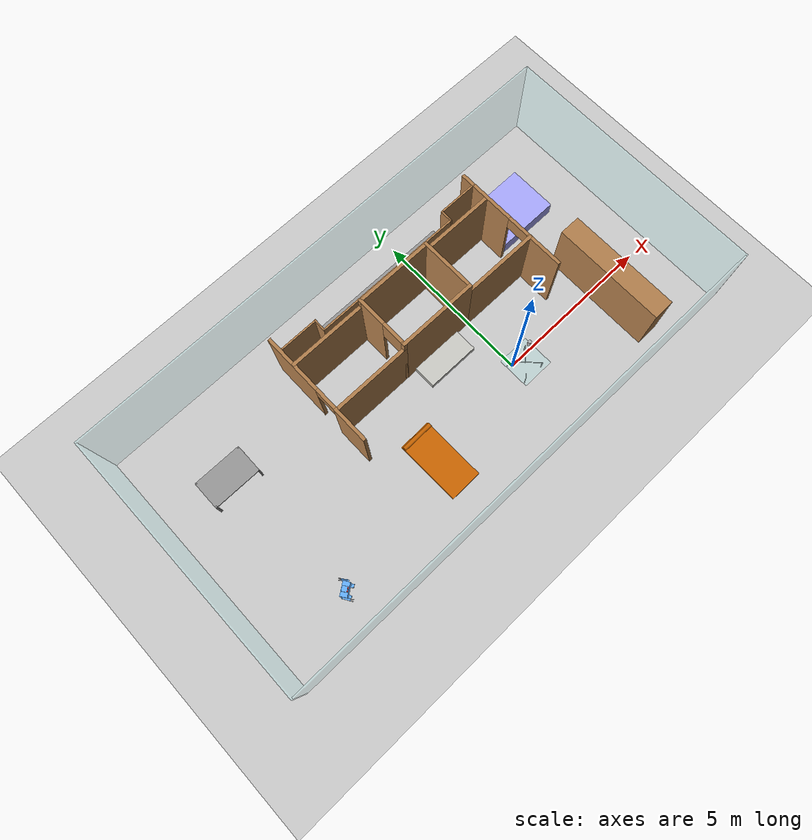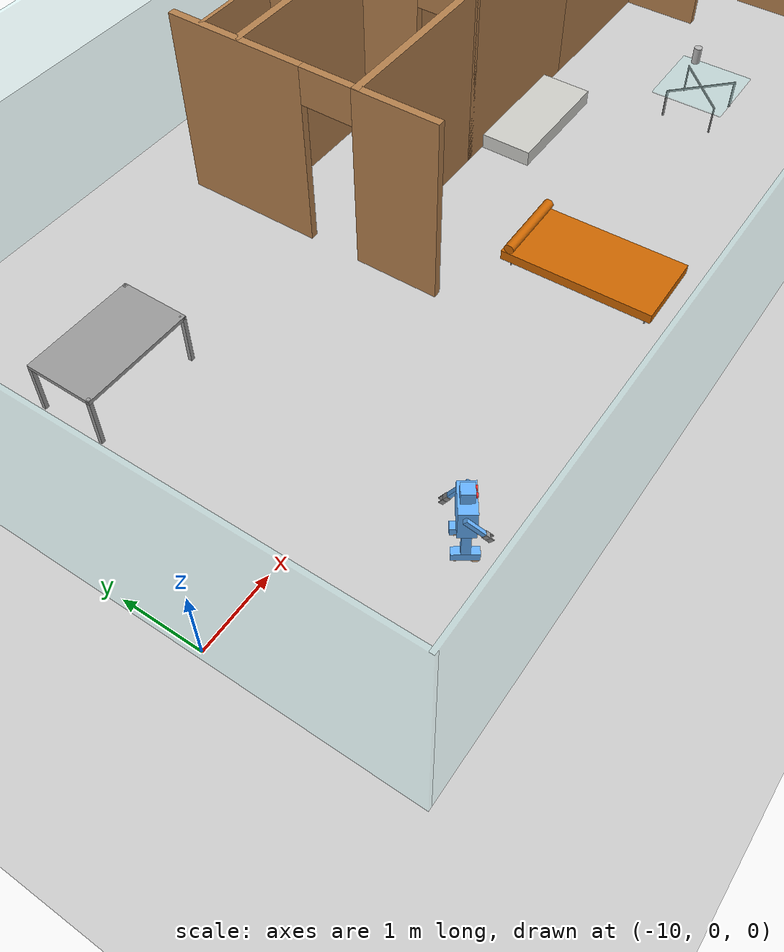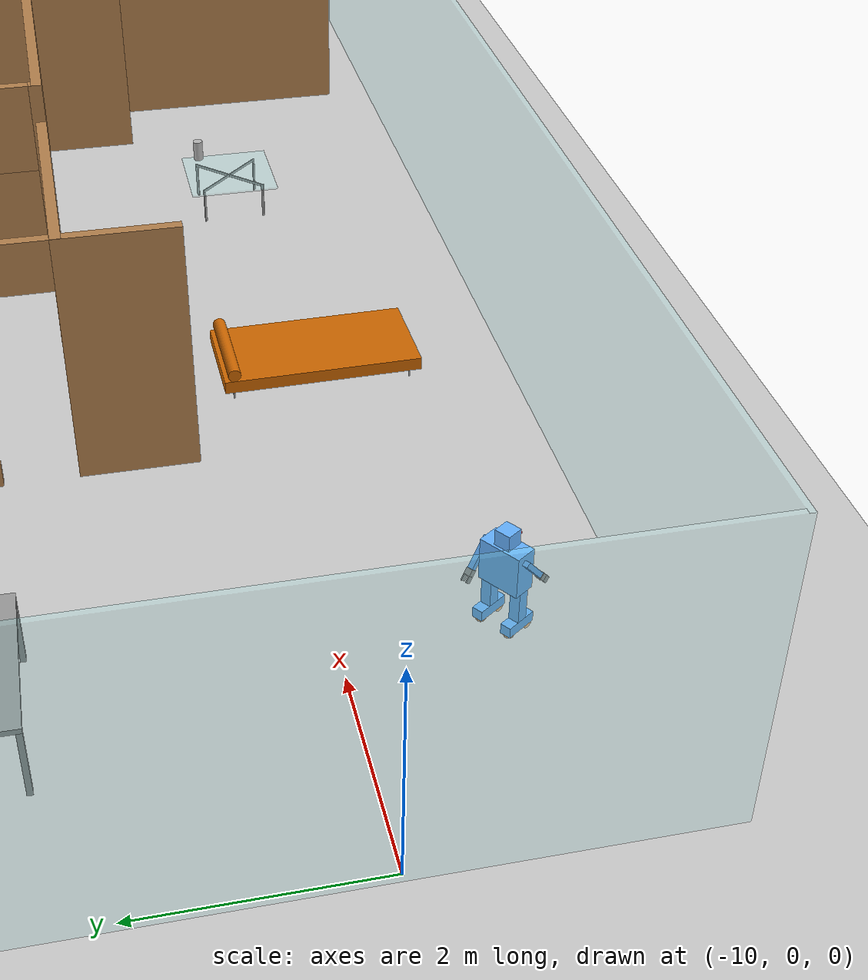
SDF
<sdf version="1.6">
 <world name="default">
  <plugin name="welcome" filename="libwelcome.so"/>
  <light name="sun" type="directional">
   <pose>0 0 10 0 -0 0</pose>
   <diffuse>0.8 0.8 0.8 1</diffuse>
   <specular>0.2 0.2 0.2 1</specular>
   <attenuation>
    <range>1000</range>
    <constant>0.9</constant>
    <linear>0.01</linear>
    <quadratic>0.001</quadratic>
   </attenuation>
   <direction>-0.5 0.1 -0.9</direction>
  </light>
  <model name="ground_plane">
   <static>1</static>
   <link name="link">
    <collision name="collision">
     <geometry><plane><normal>0 0 1</normal><size>100 100</size></plane></geometry>
     <surface><friction><ode><mu>100</mu><mu2>50</mu2></ode></friction></surface>
    </collision>
    <visual name="visual">
     <cast_shadows>0</cast_shadows>
     <geometry><plane><normal>0 0 1</normal><size>100 100</size></plane></geometry>
     <material>
      <script><uri>file://media/materials/scripts/gazebo.material</uri><name>Gazebo/Grey</name></script>
     </material>
    </visual>
   </link>
  </model>
  <gravity>0 0 -9.8</gravity>
  <magnetic_field>6e-06 2.3e-05 -4.2e-05</magnetic_field>
  <atmosphere type="adiabatic"/>
  <physics name="default_physics" default="0" type="ode">
   <max_step_size>0.001</max_step_size>
   <real_time_factor>1</real_time_factor>
   <real_time_update_rate>1000</real_time_update_rate>
  </physics>
  <scene><ambient>0.4 0.4 0.4 1</ambient><background>0.7 0.7 0.7 1</background><shadows>1</shadows></scene>
  <spherical_coordinates>
   <surface_model>EARTH_WGS84</surface_model>
   <latitude_deg>0</latitude_deg>
   <longitude_deg>0</longitude_deg>
   <elevation>0</elevation>
   <heading_deg>0</heading_deg>
  </spherical_coordinates>
  <model name="coffee_table">
   <link name="link_1">
    <pose>1.25379 -1.27559 0.12 0 -0 0.785398</pose>
    <inertial>
     <mass>1</mass>
     <inertia>
      <ixx>0.166667</ixx>
      <ixy>0</ixy>
      <ixz>0</ixz>
      <iyy>0.166667</iyy>
      <iyz>0</iyz>
      <izz>0.166667</izz>
     </inertia>
    </inertial>
    <visual name="visual">
     <geometry><box><size>0.01 0.03 0.41</size></box></geometry>
     <material>
      <lighting>1</lighting>
      <script><uri>file://media/materials/scripts/gazebo.material</uri><name>Gazebo/Grey</name></script>
      <shader type="pixel"><normal_map>__default__</normal_map></shader>
      <ambient>0.75 0.75 0.75 1</ambient>
      <diffuse>0.7 0.7 0.7 1</diffuse>
      <specular>0.01 0.01 0.01 1</specular>
      <emissive>0 0 0 1</emissive>
     </material>
    </visual>
    <collision name="collision">
     <geometry><box><size>0.01 0.03 0.41</size></box></geometry>
     <surface>
      <friction>
       <ode><mu>1</mu><mu2>1</mu2><fdir1>0 0 0</fdir1><slip1>0</slip1><slip2>0</slip2></ode>
       <torsional>
        <coefficient>1</coefficient>
        <patch_radius>0</patch_radius>
        <surface_radius>0</surface_radius>
        <use_patch_radius>1</use_patch_radius>
        <ode><slip>0</slip></ode>
       </torsional>
      </friction>
      <bounce><restitution_coefficient>0</restitution_coefficient><threshold>1e+06</threshold></bounce>
      <contact>
       <collide_without_contact>0</collide_without_contact>
       <collide_without_contact_bitmask>1</collide_without_contact_bitmask>
       <collide_bitmask>1</collide_bitmask>
       <ode>
        <soft_cfm>0</soft_cfm>
        <soft_erp>0.2</soft_erp>
        <kp>1e+13</kp>
        <kd>1</kd>
        <max_vel>0.01</max_vel>
        <min_depth>0</min_depth>
       </ode>
       <bullet>
        <split_impulse>1</split_impulse>
        <split_impulse_penetration_threshold>-0.01</split_impulse_penetration_threshold>
        <soft_cfm>0</soft_cfm>
        <soft_erp>0.2</soft_erp>
        <kp>1e+13</kp>
        <kd>1</kd>
       </bullet>
      </contact>
     </surface>
    </collision>
   </link>
   <link name="link_1_clone">
    <pose>0.567893 -0.589699 0.12 0 -0 0.785398</pose>
    <inertial>
     <mass>1</mass>
     <inertia>
      <ixx>0.166667</ixx>
      <ixy>0</ixy>
      <ixz>0</ixz>
      <iyy>0.166667</iyy>
      <iyz>0</iyz>
      <izz>0.166667</izz>
     </inertia>
    </inertial>
    <visual name="visual">
     <geometry><box><size>0.01 0.03 0.41</size></box></geometry>
     <material>
      <lighting>1</lighting>
      <script><uri>file://media/materials/scripts/gazebo.material</uri><name>Gazebo/Grey</name></script>
      <shader type="pixel"><normal_map>__default__</normal_map></shader>
      <ambient>0.75 0.75 0.75 1</ambient>
      <diffuse>0.7 0.7 0.7 1</diffuse>
      <specular>0.01 0.01 0.01 1</specular>
      <emissive>0 0 0 1</emissive>
     </material>
    </visual>
    <collision name="collision">
     <geometry><box><size>0.01 0.03 0.41</size></box></geometry>
     <surface>
      <friction>
       <ode><mu>1</mu><mu2>1</mu2><fdir1>0 0 0</fdir1><slip1>0</slip1><slip2>0</slip2></ode>
       <torsional>
        <coefficient>1</coefficient>
        <patch_radius>0</patch_radius>
        <surface_radius>0</surface_radius>
        <use_patch_radius>1</use_patch_radius>
        <ode><slip>0</slip></ode>
       </torsional>
      </friction>
      <bounce><restitution_coefficient>0</restitution_coefficient><threshold>1e+06</threshold></bounce>
      <contact>
       <collide_without_contact>0</collide_without_contact>
       <collide_without_contact_bitmask>1</collide_without_contact_bitmask>
       <collide_bitmask>1</collide_bitmask>
       <ode>
        <soft_cfm>0</soft_cfm>
        <soft_erp>0.2</soft_erp>
        <kp>1e+13</kp>
        <kd>1</kd>
        <max_vel>0.01</max_vel>
        <min_depth>0</min_depth>
       </ode>
       <bullet>
        <split_impulse>1</split_impulse>
        <split_impulse_penetration_threshold>-0.01</split_impulse_penetration_threshold>
        <soft_cfm>0</soft_cfm>
        <soft_erp>0.2</soft_erp>
        <kp>1e+13</kp>
        <kd>1</kd>
       </bullet>
      </contact>
     </surface>
    </collision>
   </link>
   <link name="link_1_clone_0">
    <pose>1.25379 -0.589699 0.12 0 0 -0.785398</pose>
    <inertial>
     <mass>1</mass>
     <inertia>
      <ixx>0.166667</ixx>
      <ixy>0</ixy>
      <ixz>0</ixz>
      <iyy>0.166667</iyy>
      <iyz>0</iyz>
      <izz>0.166667</izz>
     </inertia>
    </inertial>
    <visual name="visual">
     <geometry><box><size>0.01 0.03 0.41</size></box></geometry>
     <material>
      <lighting>1</lighting>
      <script><uri>file://media/materials/scripts/gazebo.material</uri><name>Gazebo/Grey</name></script>
      <shader type="pixel"><normal_map>__default__</normal_map></shader>
      <ambient>0.75 0.75 0.75 1</ambient>
      <diffuse>0.7 0.7 0.7 1</diffuse>
      <specular>0.01 0.01 0.01 1</specular>
      <emissive>0 0 0 1</emissive>
     </material>
    </visual>
    <collision name="collision">
     <geometry><box><size>0.01 0.03 0.41</size></box></geometry>
     <surface>
      <friction>
       <ode><mu>1</mu><mu2>1</mu2><fdir1>0 0 0</fdir1><slip1>0</slip1><slip2>0</slip2></ode>
       <torsional>
        <coefficient>1</coefficient>
        <patch_radius>0</patch_radius>
        <surface_radius>0</surface_radius>
        <use_patch_radius>1</use_patch_radius>
        <ode><slip>0</slip></ode>
       </torsional>
      </friction>
      <bounce><restitution_coefficient>0</restitution_coefficient><threshold>1e+06</threshold></bounce>
      <contact>
       <collide_without_contact>0</collide_without_contact>
       <collide_without_contact_bitmask>1</collide_without_contact_bitmask>
       <collide_bitmask>1</collide_bitmask>
       <ode>
        <soft_cfm>0</soft_cfm>
        <soft_erp>0.2</soft_erp>
        <kp>1e+13</kp>
        <kd>1</kd>
        <max_vel>0.01</max_vel>
        <min_depth>0</min_depth>
       </ode>
       <bullet>
        <split_impulse>1</split_impulse>
        <split_impulse_penetration_threshold>-0.01</split_impulse_penetration_threshold>
        <soft_cfm>0</soft_cfm>
        <soft_erp>0.2</soft_erp>
        <kp>1e+13</kp>
        <kd>1</kd>
       </bullet>
      </contact>
     </surface>
    </collision>
   </link>
   <link name="link_1_clone_0_clone">
    <pose>0.567893 -1.27559 0.12 0 0 -0.785398</pose>
    <inertial>
     <mass>1</mass>
     <inertia>
      <ixx>0.166667</ixx>
      <ixy>0</ixy>
      <ixz>0</ixz>
      <iyy>0.166667</iyy>
      <iyz>0</iyz>
      <izz>0.166667</izz>
     </inertia>
    </inertial>
    <visual name="visual">
     <geometry><box><size>0.01 0.03 0.41</size></box></geometry>
     <material>
      <lighting>1</lighting>
      <script><uri>file://media/materials/scripts/gazebo.material</uri><name>Gazebo/Grey</name></script>
      <shader type="pixel"><normal_map>__default__</normal_map></shader>
      <ambient>0.75 0.75 0.75 1</ambient>
      <diffuse>0.7 0.7 0.7 1</diffuse>
      <specular>0.01 0.01 0.01 1</specular>
      <emissive>0 0 0 1</emissive>
     </material>
    </visual>
    <collision name="collision">
     <geometry><box><size>0.01 0.03 0.41</size></box></geometry>
     <surface>
      <friction>
       <ode><mu>1</mu><mu2>1</mu2><fdir1>0 0 0</fdir1><slip1>0</slip1><slip2>0</slip2></ode>
       <torsional>
        <coefficient>1</coefficient>
        <patch_radius>0</patch_radius>
        <surface_radius>0</surface_radius>
        <use_patch_radius>1</use_patch_radius>
        <ode><slip>0</slip></ode>
       </torsional>
      </friction>
      <bounce><restitution_coefficient>0</restitution_coefficient><threshold>1e+06</threshold></bounce>
      <contact>
       <collide_without_contact>0</collide_without_contact>
       <collide_without_contact_bitmask>1</collide_without_contact_bitmask>
       <collide_bitmask>1</collide_bitmask>
       <ode>
        <soft_cfm>0</soft_cfm>
        <soft_erp>0.2</soft_erp>
        <kp>1e+13</kp>
        <kd>1</kd>
        <max_vel>0.01</max_vel>
        <min_depth>0</min_depth>
       </ode>
       <bullet>
        <split_impulse>1</split_impulse>
        <split_impulse_penetration_threshold>-0.01</split_impulse_penetration_threshold>
        <soft_cfm>0</soft_cfm>
        <soft_erp>0.2</soft_erp>
        <kp>1e+13</kp>
        <kd>1</kd>
       </bullet>
      </contact>
     </surface>
    </collision>
   </link>
   <link name="link_2">
    <pose>0.910839 -0.932646 0.31 0 -0 0.785398</pose>
    <inertial>
     <mass>1</mass>
     <inertia>
      <ixx>0.166667</ixx>
      <ixy>0</ixy>
      <ixz>0</ixz>
      <iyy>0.166667</iyy>
      <iyz>0</iyz>
      <izz>0.166667</izz>
     </inertia>
    </inertial>
    <visual name="visual">
     <geometry><box><size>0.01 1 0.03</size></box></geometry>
     <material>
      <lighting>1</lighting>
      <script><uri>file://media/materials/scripts/gazebo.material</uri><name>Gazebo/Grey</name></script>
      <shader type="pixel"><normal_map>__default__</normal_map></shader>
      <ambient>0.75 0.75 0.75 1</ambient>
      <diffuse>0.7 0.7 0.7 1</diffuse>
      <specular>0.01 0.01 0.01 1</specular>
      <emissive>0 0 0 1</emissive>
     </material>
    </visual>
    <collision name="collision">
     <geometry><box><size>0.01 1 0.03</size></box></geometry>
     <surface>
      <friction>
       <ode><mu>1</mu><mu2>1</mu2><fdir1>0 0 0</fdir1><slip1>0</slip1><slip2>0</slip2></ode>
       <torsional>
        <coefficient>1</coefficient>
        <patch_radius>0</patch_radius>
        <surface_radius>0</surface_radius>
        <use_patch_radius>1</use_patch_radius>
        <ode><slip>0</slip></ode>
       </torsional>
      </friction>
      <bounce><restitution_coefficient>0</restitution_coefficient><threshold>1e+06</threshold></bounce>
      <contact>
       <collide_without_contact>0</collide_without_contact>
       <collide_without_contact_bitmask>1</collide_without_contact_bitmask>
       <collide_bitmask>1</collide_bitmask>
       <ode>
        <soft_cfm>0</soft_cfm>
        <soft_erp>0.2</soft_erp>
        <kp>1e+13</kp>
        <kd>1</kd>
        <max_vel>0.01</max_vel>
        <min_depth>0</min_depth>
       </ode>
       <bullet>
        <split_impulse>1</split_impulse>
        <split_impulse_penetration_threshold>-0.01</split_impulse_penetration_threshold>
        <soft_cfm>0</soft_cfm>
        <soft_erp>0.2</soft_erp>
        <kp>1e+13</kp>
        <kd>1</kd>
       </bullet>
      </contact>
     </surface>
    </collision>
   </link>
   <link name="link_2_clone">
    <pose>0.910839 -0.932646 0.31 0 0 -0.785398</pose>
    <inertial>
     <mass>1</mass>
     <inertia>
      <ixx>0.166667</ixx>
      <ixy>0</ixy>
      <ixz>0</ixz>
      <iyy>0.166667</iyy>
      <iyz>0</iyz>
      <izz>0.166667</izz>
     </inertia>
    </inertial>
    <visual name="visual">
     <geometry><box><size>0.01 1 0.03</size></box></geometry>
     <material>
      <lighting>1</lighting>
      <script><uri>file://media/materials/scripts/gazebo.material</uri><name>Gazebo/Grey</name></script>
      <shader type="pixel"><normal_map>__default__</normal_map></shader>
      <ambient>0.75 0.75 0.75 1</ambient>
      <diffuse>0.7 0.7 0.7 1</diffuse>
      <specular>0.01 0.01 0.01 1</specular>
      <emissive>0 0 0 1</emissive>
     </material>
    </visual>
    <collision name="collision">
     <geometry><box><size>0.01 1 0.03</size></box></geometry>
     <surface>
      <friction>
       <ode><mu>1</mu><mu2>1</mu2><fdir1>0 0 0</fdir1><slip1>0</slip1><slip2>0</slip2></ode>
       <torsional>
        <coefficient>1</coefficient>
        <patch_radius>0</patch_radius>
        <surface_radius>0</surface_radius>
        <use_patch_radius>1</use_patch_radius>
        <ode><slip>0</slip></ode>
       </torsional>
      </friction>
      <bounce><restitution_coefficient>0</restitution_coefficient><threshold>1e+06</threshold></bounce>
      <contact>
       <collide_without_contact>0</collide_without_contact>
       <collide_without_contact_bitmask>1</collide_without_contact_bitmask>
       <collide_bitmask>1</collide_bitmask>
       <ode>
        <soft_cfm>0</soft_cfm>
        <soft_erp>0.2</soft_erp>
        <kp>1e+13</kp>
        <kd>1</kd>
        <max_vel>0.01</max_vel>
        <min_depth>0</min_depth>
       </ode>
       <bullet>
        <split_impulse>1</split_impulse>
        <split_impulse_penetration_threshold>-0.01</split_impulse_penetration_threshold>
        <soft_cfm>0</soft_cfm>
        <soft_erp>0.2</soft_erp>
        <kp>1e+13</kp>
        <kd>1</kd>
       </bullet>
      </contact>
     </surface>
    </collision>
   </link>
   <link name="link_4">
    <pose>0.910839 -0.932646 0.335 0 -0 0</pose>
    <inertial>
     <mass>1</mass>
     <inertia>
      <ixx>0.166667</ixx>
      <ixy>0</ixy>
      <ixz>0</ixz>
      <iyy>0.166667</iyy>
      <iyz>0</iyz>
      <izz>0.166667</izz>
     </inertia>
    </inertial>
    <visual name="visual">
     <geometry><box><size>1 1 0.02</size></box></geometry>
     <material>
      <lighting>1</lighting>
      <script><uri>file://media/materials/scripts/gazebo.material</uri><name>Gazebo/Grey</name></script>
      <shader type="pixel"><normal_map>__default__</normal_map></shader>
      <ambient>0.6 1 1 1</ambient>
      <diffuse>0.7 0.7 0.7 1</diffuse>
      <specular>0.01 0.01 0.01 1</specular>
      <emissive>0 0 0 1</emissive>
     </material>
     <transparency>0.85</transparency>
    </visual>
    <collision name="collision">
     <geometry><box><size>1 1 0.02</size></box></geometry>
     <surface>
      <friction>
       <ode><mu>1</mu><mu2>1</mu2><fdir1>0 0 0</fdir1><slip1>0</slip1><slip2>0</slip2></ode>
       <torsional>
        <coefficient>1</coefficient>
        <patch_radius>0</patch_radius>
        <surface_radius>0</surface_radius>
        <use_patch_radius>1</use_patch_radius>
        <ode><slip>0</slip></ode>
       </torsional>
      </friction>
      <bounce><restitution_coefficient>0</restitution_coefficient><threshold>1e+06</threshold></bounce>
      <contact>
       <collide_without_contact>0</collide_without_contact>
       <collide_without_contact_bitmask>1</collide_without_contact_bitmask>
       <collide_bitmask>1</collide_bitmask>
       <ode>
        <soft_cfm>0</soft_cfm>
        <soft_erp>0.2</soft_erp>
        <kp>1e+13</kp>
        <kd>1</kd>
        <max_vel>0.01</max_vel>
        <min_depth>0</min_depth>
       </ode>
       <bullet>
        <split_impulse>1</split_impulse>
        <split_impulse_penetration_threshold>-0.01</split_impulse_penetration_threshold>
        <soft_cfm>0</soft_cfm>
        <soft_erp>0.2</soft_erp>
        <kp>1e+13</kp>
        <kd>1</kd>
       </bullet>
      </contact>
     </surface>
    </collision>
   </link>
   <joint name="link_2_JOINT_0_0" type="fixed">
    <parent>link_2</parent>
    <child>link_4</child>
    <physics>
     <ode><limit><cfm>0</cfm><erp>0.2</erp></limit><suspension><cfm>0</cfm><erp>0.2</erp></suspension></ode>
    </physics>
   </joint>
   <joint name="link_2_JOINT_0" type="fixed">
    <parent>link_2</parent>
    <child>link_1</child>
    <physics>
     <ode><limit><cfm>0</cfm><erp>0.2</erp></limit><suspension><cfm>0</cfm><erp>0.2</erp></suspension></ode>
    </physics>
   </joint>
   <joint name="link_2_JOINT_1_0" type="fixed">
    <parent>link_2</parent>
    <child>link_2_clone</child>
    <physics>
     <ode><limit><cfm>0</cfm><erp>0.2</erp></limit><suspension><cfm>0</cfm><erp>0.2</erp></suspension></ode>
    </physics>
   </joint>
   <joint name="link_2_JOINT_1" type="fixed">
    <parent>link_2</parent>
    <child>link_1_clone</child>
    <physics>
     <ode><limit><cfm>0</cfm><erp>0.2</erp></limit><suspension><cfm>0</cfm><erp>0.2</erp></suspension></ode>
    </physics>
   </joint>
   <joint name="link_2_clone_JOINT_0" type="fixed">
    <parent>link_2_clone</parent>
    <child>link_4</child>
    <physics>
     <ode><limit><cfm>0</cfm><erp>0.2</erp></limit><suspension><cfm>0</cfm><erp>0.2</erp></suspension></ode>
    </physics>
   </joint>
   <joint name="link_2_clone_JOINT_2" type="fixed">
    <parent>link_2_clone</parent>
    <child>link_1_clone_0_clone</child>
    <physics>
     <ode><limit><cfm>0</cfm><erp>0.2</erp></limit><suspension><cfm>0</cfm><erp>0.2</erp></suspension></ode>
    </physics>
   </joint>
   <joint name="link_2_clone_JOINT_3" type="fixed">
    <parent>link_2_clone</parent>
    <child>link_1_clone_0</child>
    <physics>
     <ode><limit><cfm>0</cfm><erp>0.2</erp></limit><suspension><cfm>0</cfm><erp>0.2</erp></suspension></ode>
    </physics>
   </joint>
   <static>0</static>
   <pose>-0.68094 0.674766 0.084997 -0 -2e-06 0.006456</pose>
  </model>
  <model name="Farnsworth_House">
   <link name="Wall_0">
    <pose>0 4.05 0 0 -0 0</pose>
    <inertial>
     <mass>1</mass>
     <inertia><ixx>1</ixx><ixy>0</ixy><ixz>0</ixz><iyy>1</iyy><iyz>0</iyz><izz>1</izz></inertia>
    </inertial>
    <visual name="Wall_0_Visual">
     <pose>0 0 1.435 0 -0 0</pose>
     <geometry><box><size>15.9002 0.05 2.87</size></box></geometry>
     <material>
      <script><uri>file://media/materials/scripts/gazebo.material</uri><name>Gazebo/Grey</name></script>
      <ambient>0.6 1 1 1</ambient>
      <shader type="pixel"><normal_map>__default__</normal_map></shader>
      <diffuse>0.7 0.7 0.7 1</diffuse>
      <specular>0.01 0.01 0.01 1</specular>
      <emissive>0 0 0 1</emissive>
     </material>
     <meta><layer>0</layer></meta>
     <transparency>0.85</transparency>
    </visual>
    <collision name="Wall_0_Collision">
     <pose>0 0 1.435 0 -0 0</pose>
     <geometry><box><size>15.9002 0.05 2.87</size></box></geometry>
     <surface>
      <friction>
       <ode><mu>1</mu><mu2>1</mu2><fdir1>0 0 0</fdir1><slip1>0</slip1><slip2>0</slip2></ode>
       <torsional>
        <coefficient>1</coefficient>
        <patch_radius>0</patch_radius>
        <surface_radius>0</surface_radius>
        <use_patch_radius>1</use_patch_radius>
        <ode><slip>0</slip></ode>
       </torsional>
      </friction>
      <bounce><restitution_coefficient>0</restitution_coefficient><threshold>1e+06</threshold></bounce>
      <contact>
       <collide_without_contact>0</collide_without_contact>
       <collide_without_contact_bitmask>1</collide_without_contact_bitmask>
       <collide_bitmask>1</collide_bitmask>
       <ode>
        <soft_cfm>0</soft_cfm>
        <soft_erp>0.2</soft_erp>
        <kp>1e+13</kp>
        <kd>1</kd>
        <max_vel>0.01</max_vel>
        <min_depth>0</min_depth>
       </ode>
       <bullet>
        <split_impulse>1</split_impulse>
        <split_impulse_penetration_threshold>-0.01</split_impulse_penetration_threshold>
        <soft_cfm>0</soft_cfm>
        <soft_erp>0.2</soft_erp>
        <kp>1e+13</kp>
        <kd>1</kd>
       </bullet>
      </contact>
     </surface>
    </collision>
   </link>
   <link name="Wall_1">
    <pose>7.925 0 0 0 0 -1.5708</pose>
    <inertial>
     <mass>1</mass>
     <inertia><ixx>1</ixx><ixy>0</ixy><ixz>0</ixz><iyy>1</iyy><iyz>0</iyz><izz>1</izz></inertia>
    </inertial>
    <visual name="Wall_1_Visual">
     <pose>0 0 1.435 0 -0 0</pose>
     <geometry><box><size>8.15019 0.05 2.87</size></box></geometry>
     <material>
      <script><uri>file://media/materials/scripts/gazebo.material</uri><name>Gazebo/Grey</name></script>
      <ambient>0.6 1 1 1</ambient>
      <shader type="pixel"><normal_map>__default__</normal_map></shader>
      <diffuse>0.7 0.7 0.7 1</diffuse>
      <specular>0.01 0.01 0.01 1</specular>
      <emissive>0 0 0 1</emissive>
     </material>
     <meta><layer>0</layer></meta>
     <transparency>0.85</transparency>
    </visual>
    <collision name="Wall_1_Collision">
     <pose>0 0 1.435 0 -0 0</pose>
     <geometry><box><size>8.15019 0.05 2.87</size></box></geometry>
     <surface>
      <friction>
       <ode><mu>1</mu><mu2>1</mu2><fdir1>0 0 0</fdir1><slip1>0</slip1><slip2>0</slip2></ode>
       <torsional>
        <coefficient>1</coefficient>
        <patch_radius>0</patch_radius>
        <surface_radius>0</surface_radius>
        <use_patch_radius>1</use_patch_radius>
        <ode><slip>0</slip></ode>
       </torsional>
      </friction>
      <bounce><restitution_coefficient>0</restitution_coefficient><threshold>1e+06</threshold></bounce>
      <contact>
       <collide_without_contact>0</collide_without_contact>
       <collide_without_contact_bitmask>1</collide_without_contact_bitmask>
       <collide_bitmask>1</collide_bitmask>
       <ode>
        <soft_cfm>0</soft_cfm>
        <soft_erp>0.2</soft_erp>
        <kp>1e+13</kp>
        <kd>1</kd>
        <max_vel>0.01</max_vel>
        <min_depth>0</min_depth>
       </ode>
       <bullet>
        <split_impulse>1</split_impulse>
        <split_impulse_penetration_threshold>-0.01</split_impulse_penetration_threshold>
        <soft_cfm>0</soft_cfm>
        <soft_erp>0.2</soft_erp>
        <kp>1e+13</kp>
        <kd>1</kd>
       </bullet>
      </contact>
     </surface>
    </collision>
   </link>
   <link name="Wall_10">
    <pose>0.851 0.36 0 0 -0 0</pose>
    <visual name="Wall_10_Visual">
     <pose>0 0 1.435 0 -0 0</pose>
     <geometry><box><size>2.45 0.1 2.87</size></box></geometry>
     <material>
      <script><uri>file://media/materials/scripts/gazebo.material</uri><name>Gazebo/Wood</name></script>
      <ambient>1 1 1 1</ambient>
      <shader type="pixel"/>
      <diffuse>1 1 1 1</diffuse>
      <specular>0.2 0.2 0.2 1</specular>
      <emissive>0 0 0 1</emissive>
     </material>
     <meta><layer>0</layer></meta>
    </visual>
    <collision name="Wall_10_Collision">
     <pose>0 0 1.435 0 -0 0</pose>
     <geometry><box><size>2.45 0.1 2.87</size></box></geometry>
     <surface>
      <friction>
       <ode><mu>1</mu><mu2>1</mu2><fdir1>0 0 0</fdir1><slip1>0</slip1><slip2>0</slip2></ode>
       <torsional>
        <coefficient>1</coefficient>
        <patch_radius>0</patch_radius>
        <surface_radius>0</surface_radius>
        <use_patch_radius>1</use_patch_radius>
        <ode><slip>0</slip></ode>
       </torsional>
      </friction>
      <bounce><restitution_coefficient>0</restitution_coefficient><threshold>1e+06</threshold></bounce>
      <contact>
       <collide_without_contact>0</collide_without_contact>
       <collide_without_contact_bitmask>1</collide_without_contact_bitmask>
       <collide_bitmask>1</collide_bitmask>
       <ode>
        <soft_cfm>0</soft_cfm>
        <soft_erp>0.2</soft_erp>
        <kp>1e+13</kp>
        <kd>1</kd>
        <max_vel>0.01</max_vel>
        <min_depth>0</min_depth>
       </ode>
       <bullet>
        <split_impulse>1</split_impulse>
        <split_impulse_penetration_threshold>-0.01</split_impulse_penetration_threshold>
        <soft_cfm>0</soft_cfm>
        <soft_erp>0.2</soft_erp>
        <kp>1e+13</kp>
        <kd>1</kd>
       </bullet>
      </contact>
     </surface>
    </collision>
   </link>
   <link name="Wall_11">
    <pose>3.179 0.36 0 0 -0 0</pose>
    <visual name="Wall_11_Visual">
     <pose>0 0 1.25 0 -0 0</pose>
     <geometry><box><size>2.406 0.1 2.5</size></box></geometry>
     <material>
      <script><uri>file://media/materials/scripts/gazebo.material</uri><name>Gazebo/Wood</name></script>
      <ambient>1 1 1 1</ambient>
      <shader type="pixel"/>
      <diffuse>1 1 1 1</diffuse>
      <specular>0.2 0.2 0.2 1</specular>
      <emissive>0 0 0 1</emissive>
     </material>
     <meta><layer>0</layer></meta>
    </visual>
    <collision name="Wall_11_Collision">
     <pose>0 0 1.25 0 -0 0</pose>
     <geometry><box><size>2.406 0.1 2.5</size></box></geometry>
     <surface>
      <friction>
       <ode><mu>1</mu><mu2>1</mu2><fdir1>0 0 0</fdir1><slip1>0</slip1><slip2>0</slip2></ode>
       <torsional>
        <coefficient>1</coefficient>
        <patch_radius>0</patch_radius>
        <surface_radius>0</surface_radius>
        <use_patch_radius>1</use_patch_radius>
        <ode><slip>0</slip></ode>
       </torsional>
      </friction>
      <bounce><restitution_coefficient>0</restitution_coefficient><threshold>1e+06</threshold></bounce>
      <contact>
       <collide_without_contact>0</collide_without_contact>
       <collide_without_contact_bitmask>1</collide_without_contact_bitmask>
       <collide_bitmask>1</collide_bitmask>
       <ode>
        <soft_cfm>0</soft_cfm>
        <soft_erp>0.2</soft_erp>
        <kp>1e+13</kp>
        <kd>1</kd>
        <max_vel>0.01</max_vel>
        <min_depth>0</min_depth>
       </ode>
       <bullet>
        <split_impulse>1</split_impulse>
        <split_impulse_penetration_threshold>-0.01</split_impulse_penetration_threshold>
        <soft_cfm>0</soft_cfm>
        <soft_erp>0.2</soft_erp>
        <kp>1e+13</kp>
        <kd>1</kd>
       </bullet>
      </contact>
     </surface>
    </collision>
   </link>
   <link name="Wall_13">
    <pose>0.851 2.013 0 0 -0 0</pose>
    <visual name="Wall_13_Visual">
     <pose>0 0 1.435 0 -0 0</pose>
     <geometry><box><size>2.45 0.1 2.87</size></box></geometry>
     <material>
      <script><uri>file://media/materials/scripts/gazebo.material</uri><name>Gazebo/Wood</name></script>
      <ambient>1 1 1 1</ambient>
      <shader type="pixel"/>
      <diffuse>1 1 1 1</diffuse>
      <specular>0.2 0.2 0.2 1</specular>
      <emissive>0 0 0 1</emissive>
     </material>
     <meta><layer>0</layer></meta>
    </visual>
    <collision name="Wall_13_Collision">
     <pose>0 0 1.435 0 -0 0</pose>
     <geometry><box><size>2.45 0.1 2.87</size></box></geometry>
     <surface>
      <friction>
       <ode><mu>1</mu><mu2>1</mu2><fdir1>0 0 0</fdir1><slip1>0</slip1><slip2>0</slip2></ode>
       <torsional>
        <coefficient>1</coefficient>
        <patch_radius>0</patch_radius>
        <surface_radius>0</surface_radius>
        <use_patch_radius>1</use_patch_radius>
        <ode><slip>0</slip></ode>
       </torsional>
      </friction>
      <bounce><restitution_coefficient>0</restitution_coefficient><threshold>1e+06</threshold></bounce>
      <contact>
       <collide_without_contact>0</collide_without_contact>
       <collide_without_contact_bitmask>1</collide_without_contact_bitmask>
       <collide_bitmask>1</collide_bitmask>
       <ode>
        <soft_cfm>0</soft_cfm>
        <soft_erp>0.2</soft_erp>
        <kp>1e+13</kp>
        <kd>1</kd>
        <max_vel>0.01</max_vel>
        <min_depth>0</min_depth>
       </ode>
       <bullet>
        <split_impulse>1</split_impulse>
        <split_impulse_penetration_threshold>-0.01</split_impulse_penetration_threshold>
        <soft_cfm>0</soft_cfm>
        <soft_erp>0.2</soft_erp>
        <kp>1e+13</kp>
        <kd>1</kd>
       </bullet>
      </contact>
     </surface>
    </collision>
   </link>
   <link name="Wall_14">
    <pose>2.026 1.1865 0 0 0 -1.5708</pose>
    <visual name="Wall_14_Visual">
     <pose>0 0 1.435 0 -0 0</pose>
     <geometry><box><size>1.753 0.1 2.87</size></box></geometry>
     <material>
      <script><uri>file://media/materials/scripts/gazebo.material</uri><name>Gazebo/Wood</name></script>
      <ambient>1 1 1 1</ambient>
      <shader type="pixel"/>
      <diffuse>1 1 1 1</diffuse>
      <specular>0.2 0.2 0.2 1</specular>
      <emissive>0 0 0 1</emissive>
     </material>
     <meta><layer>0</layer></meta>
    </visual>
    <collision name="Wall_14_Collision">
     <pose>0 0 1.435 0 -0 0</pose>
     <geometry><box><size>1.753 0.1 2.87</size></box></geometry>
     <surface>
      <friction>
       <ode><mu>1</mu><mu2>1</mu2><fdir1>0 0 0</fdir1><slip1>0</slip1><slip2>0</slip2></ode>
       <torsional>
        <coefficient>1</coefficient>
        <patch_radius>0</patch_radius>
        <surface_radius>0</surface_radius>
        <use_patch_radius>1</use_patch_radius>
        <ode><slip>0</slip></ode>
       </torsional>
      </friction>
      <bounce><restitution_coefficient>0</restitution_coefficient><threshold>1e+06</threshold></bounce>
      <contact>
       <collide_without_contact>0</collide_without_contact>
       <collide_without_contact_bitmask>1</collide_without_contact_bitmask>
       <collide_bitmask>1</collide_bitmask>
       <ode>
        <soft_cfm>0</soft_cfm>
        <soft_erp>0.2</soft_erp>
        <kp>1e+13</kp>
        <kd>1</kd>
        <max_vel>0.01</max_vel>
        <min_depth>0</min_depth>
       </ode>
       <bullet>
        <split_impulse>1</split_impulse>
        <split_impulse_penetration_threshold>-0.01</split_impulse_penetration_threshold>
        <soft_cfm>0</soft_cfm>
        <soft_erp>0.2</soft_erp>
        <kp>1e+13</kp>
        <kd>1</kd>
       </bullet>
      </contact>
     </surface>
    </collision>
   </link>
   <link name="Wall_16">
    <pose>-0.324 1.1865 0 0 0 -1.5708</pose>
    <inertial>
     <mass>1</mass>
     <inertia><ixx>1</ixx><ixy>0</ixy><ixz>0</ixz><iyy>1</iyy><iyz>0</iyz><izz>1</izz></inertia>
    </inertial>
    <visual name="Wall_16_Visual_0">
     <pose>-0.414 0 1.435 0 -0 0</pose>
     <geometry><box><size>0.925 0.1 2.87</size></box></geometry>
     <material>
      <script><uri>file://media/materials/scripts/gazebo.material</uri><name>Gazebo/Wood</name></script>
      <ambient>1 1 1 1</ambient>
      <shader type="pixel"><normal_map>__default__</normal_map></shader>
      <diffuse>1 1 1 1</diffuse>
      <specular>0.2 0.2 0.2 1</specular>
      <emissive>0 0 0 1</emissive>
     </material>
     <meta><layer>0</layer></meta>
    </visual>
    <visual name="Wall_16_Visual_1">
     <pose>0.8125 0 1.435 0 -0 0</pose>
     <geometry><box><size>0.128 0.1 2.87</size></box></geometry>
     <material>
      <script><uri>file://media/materials/scripts/gazebo.material</uri><name>Gazebo/Wood</name></script>
      <ambient>1 1 1 1</ambient>
      <shader type="pixel"><normal_map>__default__</normal_map></shader>
      <diffuse>1 1 1 1</diffuse>
      <specular>0.2 0.2 0.2 1</specular>
      <emissive>0 0 0 1</emissive>
     </material>
     <meta><layer>0</layer></meta>
    </visual>
    <visual name="Wall_16_Visual_3">
     <pose>0.3985 0 2.435 0 -0 0</pose>
     <geometry><box><size>0.7 0.1 0.87</size></box></geometry>
     <material>
      <script><uri>file://media/materials/scripts/gazebo.material</uri><name>Gazebo/Wood</name></script>
      <ambient>1 1 1 1</ambient>
      <shader type="pixel"><normal_map>__default__</normal_map></shader>
      <diffuse>1 1 1 1</diffuse>
      <specular>0.2 0.2 0.2 1</specular>
      <emissive>0 0 0 1</emissive>
     </material>
     <meta><layer>0</layer></meta>
    </visual>
    <collision name="Wall_16_Collision_0">
     <pose>-0.414 0 1.435 0 -0 0</pose>
     <geometry><box><size>0.925 0.1 2.87</size></box></geometry>
     <surface>
      <friction>
       <ode><mu>1</mu><mu2>1</mu2><fdir1>0 0 0</fdir1><slip1>0</slip1><slip2>0</slip2></ode>
       <torsional>
        <coefficient>1</coefficient>
        <patch_radius>0</patch_radius>
        <surface_radius>0</surface_radius>
        <use_patch_radius>1</use_patch_radius>
        <ode><slip>0</slip></ode>
       </torsional>
      </friction>
      <bounce><restitution_coefficient>0</restitution_coefficient><threshold>1e+06</threshold></bounce>
      <contact>
       <collide_without_contact>0</collide_without_contact>
       <collide_without_contact_bitmask>1</collide_without_contact_bitmask>
       <collide_bitmask>1</collide_bitmask>
       <ode>
        <soft_cfm>0</soft_cfm>
        <soft_erp>0.2</soft_erp>
        <kp>1e+13</kp>
        <kd>1</kd>
        <max_vel>0.01</max_vel>
        <min_depth>0</min_depth>
       </ode>
       <bullet>
        <split_impulse>1</split_impulse>
        <split_impulse_penetration_threshold>-0.01</split_impulse_penetration_threshold>
        <soft_cfm>0</soft_cfm>
        <soft_erp>0.2</soft_erp>
        <kp>1e+13</kp>
        <kd>1</kd>
       </bullet>
      </contact>
     </surface>
    </collision>
    <collision name="Wall_16_Collision_1">
     <pose>0.8125 0 1.435 0 -0 0</pose>
     <geometry><box><size>0.128 0.1 2.87</size></box></geometry>
     <surface>
      <friction>
       <ode><mu>1</mu><mu2>1</mu2><fdir1>0 0 0</fdir1><slip1>0</slip1><slip2>0</slip2></ode>
       <torsional>
        <coefficient>1</coefficient>
        <patch_radius>0</patch_radius>
        <surface_radius>0</surface_radius>
        <use_patch_radius>1</use_patch_radius>
        <ode><slip>0</slip></ode>
       </torsional>
      </friction>
      <bounce><restitution_coefficient>0</restitution_coefficient><threshold>1e+06</threshold></bounce>
      <contact>
       <collide_without_contact>0</collide_without_contact>
       <collide_without_contact_bitmask>1</collide_without_contact_bitmask>
       <collide_bitmask>1</collide_bitmask>
       <ode>
        <soft_cfm>0</soft_cfm>
        <soft_erp>0.2</soft_erp>
        <kp>1e+13</kp>
        <kd>1</kd>
        <max_vel>0.01</max_vel>
        <min_depth>0</min_depth>
       </ode>
       <bullet>
        <split_impulse>1</split_impulse>
        <split_impulse_penetration_threshold>-0.01</split_impulse_penetration_threshold>
        <soft_cfm>0</soft_cfm>
        <soft_erp>0.2</soft_erp>
        <kp>1e+13</kp>
        <kd>1</kd>
       </bullet>
      </contact>
     </surface>
    </collision>
    <collision name="Wall_16_Collision_3">
     <pose>0.3985 0 2.435 0 -0 0</pose>
     <geometry><box><size>0.7 0.1 0.87</size></box></geometry>
     <surface>
      <friction>
       <ode><mu>1</mu><mu2>1</mu2><fdir1>0 0 0</fdir1><slip1>0</slip1><slip2>0</slip2></ode>
       <torsional>
        <coefficient>1</coefficient>
        <patch_radius>0</patch_radius>
        <surface_radius>0</surface_radius>
        <use_patch_radius>1</use_patch_radius>
        <ode><slip>0</slip></ode>
       </torsional>
      </friction>
      <bounce><restitution_coefficient>0</restitution_coefficient><threshold>1e+06</threshold></bounce>
      <contact>
       <collide_without_contact>0</collide_without_contact>
       <collide_without_contact_bitmask>1</collide_without_contact_bitmask>
       <collide_bitmask>1</collide_bitmask>
       <ode>
        <soft_cfm>0</soft_cfm>
        <soft_erp>0.2</soft_erp>
        <kp>1e+13</kp>
        <kd>1</kd>
        <max_vel>0.01</max_vel>
        <min_depth>0</min_depth>
       </ode>
       <bullet>
        <split_impulse>1</split_impulse>
        <split_impulse_penetration_threshold>-0.01</split_impulse_penetration_threshold>
        <soft_cfm>0</soft_cfm>
        <soft_erp>0.2</soft_erp>
        <kp>1e+13</kp>
        <kd>1</kd>
       </bullet>
      </contact>
     </surface>
    </collision>
   </link>
   <link name="Wall_18">
    <pose>-1.499 2.013 0 0 -0 3.14159</pose>
    <visual name="Wall_18_Visual">
     <pose>0 0 1.25 0 -0 0</pose>
     <geometry><box><size>2.45 0.1 2.5</size></box></geometry>
     <material>
      <script><uri>file://media/materials/scripts/gazebo.material</uri><name>Gazebo/Wood</name></script>
      <ambient>1 1 1 1</ambient>
      <shader type="pixel"/>
      <diffuse>1 1 1 1</diffuse>
      <specular>0.2 0.2 0.2 1</specular>
      <emissive>0 0 0 1</emissive>
     </material>
     <meta><layer>0</layer></meta>
    </visual>
    <collision name="Wall_18_Collision">
     <pose>0 0 1.25 0 -0 0</pose>
     <geometry><box><size>2.45 0.1 2.5</size></box></geometry>
     <surface>
      <friction>
       <ode><mu>1</mu><mu2>1</mu2><fdir1>0 0 0</fdir1><slip1>0</slip1><slip2>0</slip2></ode>
       <torsional>
        <coefficient>1</coefficient>
        <patch_radius>0</patch_radius>
        <surface_radius>0</surface_radius>
        <use_patch_radius>1</use_patch_radius>
        <ode><slip>0</slip></ode>
       </torsional>
      </friction>
      <bounce><restitution_coefficient>0</restitution_coefficient><threshold>1e+06</threshold></bounce>
      <contact>
       <collide_without_contact>0</collide_without_contact>
       <collide_without_contact_bitmask>1</collide_without_contact_bitmask>
       <collide_bitmask>1</collide_bitmask>
       <ode>
        <soft_cfm>0</soft_cfm>
        <soft_erp>0.2</soft_erp>
        <kp>1e+13</kp>
        <kd>1</kd>
        <max_vel>0.01</max_vel>
        <min_depth>0</min_depth>
       </ode>
       <bullet>
        <split_impulse>1</split_impulse>
        <split_impulse_penetration_threshold>-0.01</split_impulse_penetration_threshold>
        <soft_cfm>0</soft_cfm>
        <soft_erp>0.2</soft_erp>
        <kp>1e+13</kp>
        <kd>1</kd>
       </bullet>
      </contact>
     </surface>
    </collision>
   </link>
   <link name="Wall_2">
    <pose>0 -4.05 0 0 -0 3.14159</pose>
    <inertial>
     <mass>1</mass>
     <inertia><ixx>1</ixx><ixy>0</ixy><ixz>0</ixz><iyy>1</iyy><iyz>0</iyz><izz>1</izz></inertia>
    </inertial>
    <visual name="Wall_2_Visual">
     <pose>0 0 1.435 0 -0 0</pose>
     <geometry><box><size>15.8998 0.05 2.87</size></box></geometry>
     <material>
      <script><uri>file://media/materials/scripts/gazebo.material</uri><name>Gazebo/Grey</name></script>
      <ambient>0.6 1 1 1</ambient>
      <shader type="pixel"><normal_map>__default__</normal_map></shader>
      <diffuse>0.7 0.7 0.7 1</diffuse>
      <specular>0.01 0.01 0.01 1</specular>
      <emissive>0 0 0 1</emissive>
     </material>
     <meta><layer>0</layer></meta>
     <transparency>0.85</transparency>
    </visual>
    <collision name="Wall_2_Collision">
     <pose>0 0 1.435 0 -0 0</pose>
     <geometry><box><size>15.8998 0.05 2.87</size></box></geometry>
     <surface>
      <friction>
       <ode><mu>1</mu><mu2>1</mu2><fdir1>0 0 0</fdir1><slip1>0</slip1><slip2>0</slip2></ode>
       <torsional>
        <coefficient>1</coefficient>
        <patch_radius>0</patch_radius>
        <surface_radius>0</surface_radius>
        <use_patch_radius>1</use_patch_radius>
        <ode><slip>0</slip></ode>
       </torsional>
      </friction>
      <bounce><restitution_coefficient>0</restitution_coefficient><threshold>1e+06</threshold></bounce>
      <contact>
       <collide_without_contact>0</collide_without_contact>
       <collide_without_contact_bitmask>1</collide_without_contact_bitmask>
       <collide_bitmask>1</collide_bitmask>
       <ode>
        <soft_cfm>0</soft_cfm>
        <soft_erp>0.2</soft_erp>
        <kp>1e+13</kp>
        <kd>1</kd>
        <max_vel>0.01</max_vel>
        <min_depth>0</min_depth>
       </ode>
       <bullet>
        <split_impulse>1</split_impulse>
        <split_impulse_penetration_threshold>-0.01</split_impulse_penetration_threshold>
        <soft_cfm>0</soft_cfm>
        <soft_erp>0.2</soft_erp>
        <kp>1e+13</kp>
        <kd>1</kd>
       </bullet>
      </contact>
     </surface>
    </collision>
   </link>
   <link name="Wall_20">
    <pose>3.175 2.013 0 0 -0 0</pose>
    <visual name="Wall_20_Visual">
     <pose>0 0 1.25 0 -0 0</pose>
     <geometry><box><size>2.398 0.1 2.5</size></box></geometry>
     <material>
      <script><uri>file://media/materials/scripts/gazebo.material</uri><name>Gazebo/Wood</name></script>
      <ambient>1 1 1 1</ambient>
      <shader type="pixel"/>
      <diffuse>1 1 1 1</diffuse>
      <specular>0.2 0.2 0.2 1</specular>
      <emissive>0 0 0 1</emissive>
     </material>
     <meta><layer>0</layer></meta>
    </visual>
    <collision name="Wall_20_Collision">
     <pose>0 0 1.25 0 -0 0</pose>
     <geometry><box><size>2.398 0.1 2.5</size></box></geometry>
     <surface>
      <friction>
       <ode><mu>1</mu><mu2>1</mu2><fdir1>0 0 0</fdir1><slip1>0</slip1><slip2>0</slip2></ode>
       <torsional>
        <coefficient>1</coefficient>
        <patch_radius>0</patch_radius>
        <surface_radius>0</surface_radius>
        <use_patch_radius>1</use_patch_radius>
        <ode><slip>0</slip></ode>
       </torsional>
      </friction>
      <bounce><restitution_coefficient>0</restitution_coefficient><threshold>1e+06</threshold></bounce>
      <contact>
       <collide_without_contact>0</collide_without_contact>
       <collide_without_contact_bitmask>1</collide_without_contact_bitmask>
       <collide_bitmask>1</collide_bitmask>
       <ode>
        <soft_cfm>0</soft_cfm>
        <soft_erp>0.2</soft_erp>
        <kp>1e+13</kp>
        <kd>1</kd>
        <max_vel>0.01</max_vel>
        <min_depth>0</min_depth>
       </ode>
       <bullet>
        <split_impulse>1</split_impulse>
        <split_impulse_penetration_threshold>-0.01</split_impulse_penetration_threshold>
        <soft_cfm>0</soft_cfm>
        <soft_erp>0.2</soft_erp>
        <kp>1e+13</kp>
        <kd>1</kd>
       </bullet>
      </contact>
     </surface>
    </collision>
   </link>
   <link name="Wall_27">
    <pose>-2.084 2.54 0 0 -0 0</pose>
    <visual name="Wall_27_Visual">
     <pose>0 0 1.25 0 -0 0</pose>
     <geometry><box><size>1.25 0.05 2.5</size></box></geometry>
     <material>
      <script><uri>file://media/materials/scripts/gazebo.material</uri><name>Gazebo/Wood</name></script>
      <ambient>1 1 1 1</ambient>
      <shader type="pixel"/>
      <diffuse>1 1 1 1</diffuse>
      <specular>0.2 0.2 0.2 1</specular>
      <emissive>0 0 0 1</emissive>
     </material>
     <meta><layer>0</layer></meta>
    </visual>
    <collision name="Wall_27_Collision">
     <pose>0 0 1.25 0 -0 0</pose>
     <geometry><box><size>1.25 0.05 2.5</size></box></geometry>
     <surface>
      <friction>
       <ode><mu>1</mu><mu2>1</mu2><fdir1>0 0 0</fdir1><slip1>0</slip1><slip2>0</slip2></ode>
       <torsional>
        <coefficient>1</coefficient>
        <patch_radius>0</patch_radius>
        <surface_radius>0</surface_radius>
        <use_patch_radius>1</use_patch_radius>
        <ode><slip>0</slip></ode>
       </torsional>
      </friction>
      <bounce><restitution_coefficient>0</restitution_coefficient><threshold>1e+06</threshold></bounce>
      <contact>
       <collide_without_contact>0</collide_without_contact>
       <collide_without_contact_bitmask>1</collide_without_contact_bitmask>
       <collide_bitmask>1</collide_bitmask>
       <ode>
        <soft_cfm>0</soft_cfm>
        <soft_erp>0.2</soft_erp>
        <kp>1e+13</kp>
        <kd>1</kd>
        <max_vel>0.01</max_vel>
        <min_depth>0</min_depth>
       </ode>
       <bullet>
        <split_impulse>1</split_impulse>
        <split_impulse_penetration_threshold>-0.01</split_impulse_penetration_threshold>
        <soft_cfm>0</soft_cfm>
        <soft_erp>0.2</soft_erp>
        <kp>1e+13</kp>
        <kd>1</kd>
       </bullet>
      </contact>
     </surface>
    </collision>
   </link>
   <link name="Wall_29">
    <pose>3.724 2.54 0 0 -0 0</pose>
    <visual name="Wall_29_Visual">
     <pose>0 0 1.25 0 -0 0</pose>
     <geometry><box><size>1.25 0.05 2.5</size></box></geometry>
     <material>
      <script><uri>file://media/materials/scripts/gazebo.material</uri><name>Gazebo/Wood</name></script>
      <ambient>1 1 1 1</ambient>
      <shader type="pixel"/>
      <diffuse>1 1 1 1</diffuse>
      <specular>0.2 0.2 0.2 1</specular>
      <emissive>0 0 0 1</emissive>
     </material>
     <meta><layer>0</layer></meta>
    </visual>
    <collision name="Wall_29_Collision">
     <pose>0 0 1.25 0 -0 0</pose>
     <geometry><box><size>1.25 0.05 2.5</size></box></geometry>
     <surface>
      <friction>
       <ode><mu>1</mu><mu2>1</mu2><fdir1>0 0 0</fdir1><slip1>0</slip1><slip2>0</slip2></ode>
       <torsional>
        <coefficient>1</coefficient>
        <patch_radius>0</patch_radius>
        <surface_radius>0</surface_radius>
        <use_patch_radius>1</use_patch_radius>
        <ode><slip>0</slip></ode>
       </torsional>
      </friction>
      <bounce><restitution_coefficient>0</restitution_coefficient><threshold>1e+06</threshold></bounce>
      <contact>
       <collide_without_contact>0</collide_without_contact>
       <collide_without_contact_bitmask>1</collide_without_contact_bitmask>
       <collide_bitmask>1</collide_bitmask>
       <ode>
        <soft_cfm>0</soft_cfm>
        <soft_erp>0.2</soft_erp>
        <kp>1e+13</kp>
        <kd>1</kd>
        <max_vel>0.01</max_vel>
        <min_depth>0</min_depth>
       </ode>
       <bullet>
        <split_impulse>1</split_impulse>
        <split_impulse_penetration_threshold>-0.01</split_impulse_penetration_threshold>
        <soft_cfm>0</soft_cfm>
        <soft_erp>0.2</soft_erp>
        <kp>1e+13</kp>
        <kd>1</kd>
       </bullet>
      </contact>
     </surface>
    </collision>
   </link>
   <link name="Wall_3">
    <pose>-7.925 0 0 0 -0 1.5708</pose>
    <inertial>
     <mass>1</mass>
     <inertia><ixx>1</ixx><ixy>0</ixy><ixz>0</ixz><iyy>1</iyy><iyz>0</iyz><izz>1</izz></inertia>
    </inertial>
    <visual name="Wall_3_Visual_0">
     <pose>0 0 1.435 0 -0 0</pose>
     <geometry><box><size>8.15019 0.05 2.87</size></box></geometry>
     <material>
      <script><uri>file://media/materials/scripts/gazebo.material</uri><name>Gazebo/Grey</name></script>
      <ambient>0.6 1 1 1</ambient>
      <shader type="pixel"><normal_map>__default__</normal_map></shader>
      <diffuse>0.7 0.7 0.7 1</diffuse>
      <specular>0.01 0.01 0.01 1</specular>
      <emissive>0 0 0 1</emissive>
     </material>
     <meta><layer>0</layer></meta>
     <transparency>0.85</transparency>
    </visual>
    <collision name="Wall_3_Collision_0">
     <pose>0 0 1.435 0 -0 0</pose>
     <geometry><box><size>8.15019 0.05 2.87</size></box></geometry>
     <surface>
      <friction>
       <ode><mu>1</mu><mu2>1</mu2><fdir1>0 0 0</fdir1><slip1>0</slip1><slip2>0</slip2></ode>
       <torsional>
        <coefficient>1</coefficient>
        <patch_radius>0</patch_radius>
        <surface_radius>0</surface_radius>
        <use_patch_radius>1</use_patch_radius>
        <ode><slip>0</slip></ode>
       </torsional>
      </friction>
      <bounce><restitution_coefficient>0</restitution_coefficient><threshold>1e+06</threshold></bounce>
      <contact>
       <collide_without_contact>0</collide_without_contact>
       <collide_without_contact_bitmask>1</collide_without_contact_bitmask>
       <collide_bitmask>1</collide_bitmask>
       <ode>
        <soft_cfm>0</soft_cfm>
        <soft_erp>0.2</soft_erp>
        <kp>1e+13</kp>
        <kd>1</kd>
        <max_vel>0.01</max_vel>
        <min_depth>0</min_depth>
       </ode>
       <bullet>
        <split_impulse>1</split_impulse>
        <split_impulse_penetration_threshold>-0.01</split_impulse_penetration_threshold>
        <soft_cfm>0</soft_cfm>
        <soft_erp>0.2</soft_erp>
        <kp>1e+13</kp>
        <kd>1</kd>
       </bullet>
      </contact>
     </surface>
    </collision>
   </link>
   <link name="Wall_31">
    <pose>-1.484 2.365 0 0 0 -1.5708</pose>
    <visual name="Wall_31_Visual">
     <pose>0 0 1.25 0 -0 0</pose>
     <geometry><box><size>0.4 0.05 2.5</size></box></geometry>
     <material>
      <script><uri>file://media/materials/scripts/gazebo.material</uri><name>Gazebo/Wood</name></script>
      <ambient>1 1 1 1</ambient>
      <shader type="pixel"/>
      <diffuse>1 1 1 1</diffuse>
      <specular>0.2 0.2 0.2 1</specular>
      <emissive>0 0 0 1</emissive>
     </material>
     <meta><layer>0</layer></meta>
    </visual>
    <collision name="Wall_31_Collision">
     <pose>0 0 1.25 0 -0 0</pose>
     <geometry><box><size>0.4 0.05 2.5</size></box></geometry>
     <surface>
      <friction>
       <ode><mu>1</mu><mu2>1</mu2><fdir1>0 0 0</fdir1><slip1>0</slip1><slip2>0</slip2></ode>
       <torsional>
        <coefficient>1</coefficient>
        <patch_radius>0</patch_radius>
        <surface_radius>0</surface_radius>
        <use_patch_radius>1</use_patch_radius>
        <ode><slip>0</slip></ode>
       </torsional>
      </friction>
      <bounce><restitution_coefficient>0</restitution_coefficient><threshold>1e+06</threshold></bounce>
      <contact>
       <collide_without_contact>0</collide_without_contact>
       <collide_without_contact_bitmask>1</collide_without_contact_bitmask>
       <collide_bitmask>1</collide_bitmask>
       <ode>
        <soft_cfm>0</soft_cfm>
        <soft_erp>0.2</soft_erp>
        <kp>1e+13</kp>
        <kd>1</kd>
        <max_vel>0.01</max_vel>
        <min_depth>0</min_depth>
       </ode>
       <bullet>
        <split_impulse>1</split_impulse>
        <split_impulse_penetration_threshold>-0.01</split_impulse_penetration_threshold>
        <soft_cfm>0</soft_cfm>
        <soft_erp>0.2</soft_erp>
        <kp>1e+13</kp>
        <kd>1</kd>
       </bullet>
      </contact>
     </surface>
    </collision>
   </link>
   <link name="Wall_32">
    <pose>0.82 2.19 0 0 -0 0</pose>
    <visual name="Wall_32_Visual">
     <pose>0 0 1.25 0 -0 0</pose>
     <geometry><box><size>4.658 0.05 2.5</size></box></geometry>
     <material>
      <script><uri>file://media/materials/scripts/gazebo.material</uri><name>Gazebo/Wood</name></script>
      <ambient>1 1 1 1</ambient>
      <shader type="pixel"/>
      <diffuse>1 1 1 1</diffuse>
      <specular>0.2 0.2 0.2 1</specular>
      <emissive>0 0 0 1</emissive>
     </material>
     <meta><layer>0</layer></meta>
    </visual>
    <collision name="Wall_32_Collision">
     <pose>0 0 1.25 0 -0 0</pose>
     <geometry><box><size>4.658 0.05 2.5</size></box></geometry>
     <surface>
      <friction>
       <ode><mu>1</mu><mu2>1</mu2><fdir1>0 0 0</fdir1><slip1>0</slip1><slip2>0</slip2></ode>
       <torsional>
        <coefficient>1</coefficient>
        <patch_radius>0</patch_radius>
        <surface_radius>0</surface_radius>
        <use_patch_radius>1</use_patch_radius>
        <ode><slip>0</slip></ode>
       </torsional>
      </friction>
      <bounce><restitution_coefficient>0</restitution_coefficient><threshold>1e+06</threshold></bounce>
      <contact>
       <collide_without_contact>0</collide_without_contact>
       <collide_without_contact_bitmask>1</collide_without_contact_bitmask>
       <collide_bitmask>1</collide_bitmask>
       <ode>
        <soft_cfm>0</soft_cfm>
        <soft_erp>0.2</soft_erp>
        <kp>1e+13</kp>
        <kd>1</kd>
        <max_vel>0.01</max_vel>
        <min_depth>0</min_depth>
       </ode>
       <bullet>
        <split_impulse>1</split_impulse>
        <split_impulse_penetration_threshold>-0.01</split_impulse_penetration_threshold>
        <soft_cfm>0</soft_cfm>
        <soft_erp>0.2</soft_erp>
        <kp>1e+13</kp>
        <kd>1</kd>
       </bullet>
      </contact>
     </surface>
    </collision>
   </link>
   <link name="Wall_33">
    <pose>3.124 2.365 0 0 -0 1.5708</pose>
    <visual name="Wall_33_Visual">
     <pose>0 0 1.25 0 -0 0</pose>
     <geometry><box><size>0.4 0.05 2.5</size></box></geometry>
     <material>
      <script><uri>file://media/materials/scripts/gazebo.material</uri><name>Gazebo/Wood</name></script>
      <ambient>1 1 1 1</ambient>
      <shader type="pixel"/>
      <diffuse>1 1 1 1</diffuse>
      <specular>0.2 0.2 0.2 1</specular>
      <emissive>0 0 0 1</emissive>
     </material>
     <meta><layer>0</layer></meta>
    </visual>
    <collision name="Wall_33_Collision">
     <pose>0 0 1.25 0 -0 0</pose>
     <geometry><box><size>0.4 0.05 2.5</size></box></geometry>
     <surface>
      <friction>
       <ode><mu>1</mu><mu2>1</mu2><fdir1>0 0 0</fdir1><slip1>0</slip1><slip2>0</slip2></ode>
       <torsional>
        <coefficient>1</coefficient>
        <patch_radius>0</patch_radius>
        <surface_radius>0</surface_radius>
        <use_patch_radius>1</use_patch_radius>
        <ode><slip>0</slip></ode>
       </torsional>
      </friction>
      <bounce><restitution_coefficient>0</restitution_coefficient><threshold>1e+06</threshold></bounce>
      <contact>
       <collide_without_contact>0</collide_without_contact>
       <collide_without_contact_bitmask>1</collide_without_contact_bitmask>
       <collide_bitmask>1</collide_bitmask>
       <ode>
        <soft_cfm>0</soft_cfm>
        <soft_erp>0.2</soft_erp>
        <kp>1e+13</kp>
        <kd>1</kd>
        <max_vel>0.01</max_vel>
        <min_depth>0</min_depth>
       </ode>
       <bullet>
        <split_impulse>1</split_impulse>
        <split_impulse_penetration_threshold>-0.01</split_impulse_penetration_threshold>
        <soft_cfm>0</soft_cfm>
        <soft_erp>0.2</soft_erp>
        <kp>1e+13</kp>
        <kd>1</kd>
       </bullet>
      </contact>
     </surface>
    </collision>
   </link>
   <link name="Wall_37">
    <pose>0.8245 2.534 0 0 -0 0</pose>
    <visual name="Wall_37_Visual">
     <pose>0 0 0.5 0 -0 0</pose>
     <geometry><box><size>4.55152 0.6 1</size></box></geometry>
     <material>
      <script><uri>file://media/materials/scripts/gazebo.material</uri><name>Gazebo/Grey</name></script>
      <ambient>1 1 1 1</ambient>
      <shader type="pixel"/>
      <diffuse>0.7 0.7 0.7 1</diffuse>
      <specular>0.01 0.01 0.01 1</specular>
      <emissive>0 0 0 1</emissive>
     </material>
     <meta><layer>0</layer></meta>
    </visual>
    <collision name="Wall_37_Collision">
     <pose>0 0 0.5 0 -0 0</pose>
     <geometry><box><size>4.55152 0.6 1</size></box></geometry>
     <surface>
      <friction>
       <ode><mu>1</mu><mu2>1</mu2><fdir1>0 0 0</fdir1><slip1>0</slip1><slip2>0</slip2></ode>
       <torsional>
        <coefficient>1</coefficient>
        <patch_radius>0</patch_radius>
        <surface_radius>0</surface_radius>
        <use_patch_radius>1</use_patch_radius>
        <ode><slip>0</slip></ode>
       </torsional>
      </friction>
      <bounce><restitution_coefficient>0</restitution_coefficient><threshold>1e+06</threshold></bounce>
      <contact>
       <collide_without_contact>0</collide_without_contact>
       <collide_without_contact_bitmask>1</collide_without_contact_bitmask>
       <collide_bitmask>1</collide_bitmask>
       <ode>
        <soft_cfm>0</soft_cfm>
        <soft_erp>0.2</soft_erp>
        <kp>1e+13</kp>
        <kd>1</kd>
        <max_vel>0.01</max_vel>
        <min_depth>0</min_depth>
       </ode>
       <bullet>
        <split_impulse>1</split_impulse>
        <split_impulse_penetration_threshold>-0.01</split_impulse_penetration_threshold>
        <soft_cfm>0</soft_cfm>
        <soft_erp>0.2</soft_erp>
        <kp>1e+13</kp>
        <kd>1</kd>
       </bullet>
      </contact>
     </surface>
    </collision>
   </link>
   <link name="Wall_39">
    <pose>0.828 -0.04 0 0 -0 0</pose>
    <visual name="Wall_39_Visual">
     <pose>0 0 0.05 0 -0 0</pose>
     <geometry><box><size>1.63986 0.7 0.3</size></box></geometry>
     <material>
      <script><uri>file://media/materials/scripts/gazebo.material</uri><name>Gazebo/CeilingTiled</name></script>
      <ambient>1 1 1 1</ambient>
      <shader type="pixel"/>
      <diffuse>1 1 1 1</diffuse>
      <specular>0 0 0 1</specular>
      <emissive>0 0 0 1</emissive>
     </material>
     <meta><layer>0</layer></meta>
    </visual>
    <collision name="Wall_39_Collision">
     <pose>0 0 0.05 0 -0 0</pose>
     <geometry><box><size>1.63986 0.7 0.3</size></box></geometry>
     <surface>
      <friction>
       <ode><mu>1</mu><mu2>1</mu2><fdir1>0 0 0</fdir1><slip1>0</slip1><slip2>0</slip2></ode>
       <torsional>
        <coefficient>1</coefficient>
        <patch_radius>0</patch_radius>
        <surface_radius>0</surface_radius>
        <use_patch_radius>1</use_patch_radius>
        <ode><slip>0</slip></ode>
       </torsional>
      </friction>
      <bounce><restitution_coefficient>0</restitution_coefficient><threshold>1e+06</threshold></bounce>
      <contact>
       <collide_without_contact>0</collide_without_contact>
       <collide_without_contact_bitmask>1</collide_without_contact_bitmask>
       <collide_bitmask>1</collide_bitmask>
       <ode>
        <soft_cfm>0</soft_cfm>
        <soft_erp>0.2</soft_erp>
        <kp>1e+13</kp>
        <kd>1</kd>
        <max_vel>0.01</max_vel>
        <min_depth>0</min_depth>
       </ode>
       <bullet>
        <split_impulse>1</split_impulse>
        <split_impulse_penetration_threshold>-0.01</split_impulse_penetration_threshold>
        <soft_cfm>0</soft_cfm>
        <soft_erp>0.2</soft_erp>
        <kp>1e+13</kp>
        <kd>1</kd>
       </bullet>
      </contact>
     </surface>
    </collision>
   </link>
   <link name="Wall_41">
    <pose>5.603 -1.768 0 0 0 -1.5708</pose>
    <visual name="Wall_41_Visual">
     <pose>0 0 1 0 -0 0</pose>
     <geometry><box><size>3.5 0.65 2</size></box></geometry>
     <material>
      <script><uri>file://media/materials/scripts/gazebo.material</uri><name>Gazebo/Wood</name></script>
      <ambient>1 1 1 1</ambient>
      <shader type="pixel"/>
      <diffuse>1 1 1 1</diffuse>
      <specular>0.2 0.2 0.2 1</specular>
      <emissive>0 0 0 1</emissive>
     </material>
     <meta><layer>0</layer></meta>
    </visual>
    <collision name="Wall_41_Collision">
     <pose>0 0 1 0 -0 0</pose>
     <geometry><box><size>3.5 0.65 2</size></box></geometry>
     <surface>
      <friction>
       <ode><mu>1</mu><mu2>1</mu2><fdir1>0 0 0</fdir1><slip1>0</slip1><slip2>0</slip2></ode>
       <torsional>
        <coefficient>1</coefficient>
        <patch_radius>0</patch_radius>
        <surface_radius>0</surface_radius>
        <use_patch_radius>1</use_patch_radius>
        <ode><slip>0</slip></ode>
       </torsional>
      </friction>
      <bounce><restitution_coefficient>0</restitution_coefficient><threshold>1e+06</threshold></bounce>
      <contact>
       <collide_without_contact>0</collide_without_contact>
       <collide_without_contact_bitmask>1</collide_without_contact_bitmask>
       <collide_bitmask>1</collide_bitmask>
       <ode>
        <soft_cfm>0</soft_cfm>
        <soft_erp>0.2</soft_erp>
        <kp>1e+13</kp>
        <kd>1</kd>
        <max_vel>0.01</max_vel>
        <min_depth>0</min_depth>
       </ode>
       <bullet>
        <split_impulse>1</split_impulse>
        <split_impulse_penetration_threshold>-0.01</split_impulse_penetration_threshold>
        <soft_cfm>0</soft_cfm>
        <soft_erp>0.2</soft_erp>
        <kp>1e+13</kp>
        <kd>1</kd>
       </bullet>
      </contact>
     </surface>
    </collision>
   </link>
   <link name="Wall_43">
    <pose>5.41642 1.96377 0 0 -0 0</pose>
    <visual name="Wall_43_Visual">
     <pose>0 0 0.25 0 -0 0</pose>
     <geometry><box><size>2.03 1.52 0.5</size></box></geometry>
     <material>
      <script><uri>file://media/materials/scripts/gazebo.material</uri><name>Gazebo/Grey</name></script>
      <ambient>0.666667 0.666667 1 1</ambient>
      <shader type="pixel"/>
      <diffuse>0.7 0.7 0.7 1</diffuse>
      <specular>0.01 0.01 0.01 1</specular>
      <emissive>0 0 0 1</emissive>
     </material>
     <meta><layer>0</layer></meta>
    </visual>
    <collision name="Wall_43_Collision">
     <pose>0 0 0.25 0 -0 0</pose>
     <geometry><box><size>2.03 1.52 0.5</size></box></geometry>
     <surface>
      <friction>
       <ode><mu>1</mu><mu2>1</mu2><fdir1>0 0 0</fdir1><slip1>0</slip1><slip2>0</slip2></ode>
       <torsional>
        <coefficient>1</coefficient>
        <patch_radius>0</patch_radius>
        <surface_radius>0</surface_radius>
        <use_patch_radius>1</use_patch_radius>
        <ode><slip>0</slip></ode>
       </torsional>
      </friction>
      <bounce><restitution_coefficient>0</restitution_coefficient><threshold>1e+06</threshold></bounce>
      <contact>
       <collide_without_contact>0</collide_without_contact>
       <collide_without_contact_bitmask>1</collide_without_contact_bitmask>
       <collide_bitmask>1</collide_bitmask>
       <ode>
        <soft_cfm>0</soft_cfm>
        <soft_erp>0.2</soft_erp>
        <kp>1e+13</kp>
        <kd>1</kd>
        <max_vel>0.01</max_vel>
        <min_depth>0</min_depth>
       </ode>
       <bullet>
        <split_impulse>1</split_impulse>
        <split_impulse_penetration_threshold>-0.01</split_impulse_penetration_threshold>
        <soft_cfm>0</soft_cfm>
        <soft_erp>0.2</soft_erp>
        <kp>1e+13</kp>
        <kd>1</kd>
       </bullet>
      </contact>
     </surface>
    </collision>
   </link>
   <link name="Wall_5">
    <pose>-2.694 1.128 0 0 0 -1.5708</pose>
    <inertial>
     <mass>1</mass>
     <inertia><ixx>1</ixx><ixy>0</ixy><ixz>0</ixz><iyy>1</iyy><iyz>0</iyz><izz>1</izz></inertia>
    </inertial>
    <visual name="Wall_5_Visual_0">
     <pose>-0.916961 0 1.25 0 -0 0</pose>
     <geometry><box><size>1.86591 0.1 2.5</size></box></geometry>
     <material>
      <script><uri>file://media/materials/scripts/gazebo.material</uri><name>Gazebo/Wood</name></script>
      <ambient>1 1 1 1</ambient>
      <shader type="pixel"><normal_map>__default__</normal_map></shader>
      <diffuse>1 1 1 1</diffuse>
      <specular>0.2 0.2 0.2 1</specular>
      <emissive>0 0 0 1</emissive>
     </material>
     <meta><layer>0</layer></meta>
    </visual>
    <visual name="Wall_5_Visual_1">
     <pose>1.28295 0 1.25 0 -0 0</pose>
     <geometry><box><size>1.13392 0.1 2.5</size></box></geometry>
     <material>
      <script><uri>file://media/materials/scripts/gazebo.material</uri><name>Gazebo/Wood</name></script>
      <ambient>1 1 1 1</ambient>
      <shader type="pixel"><normal_map>__default__</normal_map></shader>
      <diffuse>1 1 1 1</diffuse>
      <specular>0.2 0.2 0.2 1</specular>
      <emissive>0 0 0 1</emissive>
     </material>
     <meta><layer>0</layer></meta>
    </visual>
    <visual name="Wall_5_Visual_2">
     <pose>0.365993 0 2.25 0 -0 0</pose>
     <geometry><box><size>0.7 0.1 0.5</size></box></geometry>
     <material>
      <script><uri>file://media/materials/scripts/gazebo.material</uri><name>Gazebo/Wood</name></script>
      <ambient>1 1 1 1</ambient>
      <shader type="pixel"><normal_map>__default__</normal_map></shader>
      <diffuse>1 1 1 1</diffuse>
      <specular>0.2 0.2 0.2 1</specular>
      <emissive>0 0 0 1</emissive>
     </material>
     <meta><layer>0</layer></meta>
    </visual>
    <collision name="Wall_5_Collision_0">
     <pose>-0.916961 0 1.25 0 -0 0</pose>
     <geometry><box><size>1.86591 0.1 2.5</size></box></geometry>
     <surface>
      <friction>
       <ode><mu>1</mu><mu2>1</mu2><fdir1>0 0 0</fdir1><slip1>0</slip1><slip2>0</slip2></ode>
       <torsional>
        <coefficient>1</coefficient>
        <patch_radius>0</patch_radius>
        <surface_radius>0</surface_radius>
        <use_patch_radius>1</use_patch_radius>
        <ode><slip>0</slip></ode>
       </torsional>
      </friction>
      <bounce><restitution_coefficient>0</restitution_coefficient><threshold>1e+06</threshold></bounce>
      <contact>
       <collide_without_contact>0</collide_without_contact>
       <collide_without_contact_bitmask>1</collide_without_contact_bitmask>
       <collide_bitmask>1</collide_bitmask>
       <ode>
        <soft_cfm>0</soft_cfm>
        <soft_erp>0.2</soft_erp>
        <kp>1e+13</kp>
        <kd>1</kd>
        <max_vel>0.01</max_vel>
        <min_depth>0</min_depth>
       </ode>
       <bullet>
        <split_impulse>1</split_impulse>
        <split_impulse_penetration_threshold>-0.01</split_impulse_penetration_threshold>
        <soft_cfm>0</soft_cfm>
        <soft_erp>0.2</soft_erp>
        <kp>1e+13</kp>
        <kd>1</kd>
       </bullet>
      </contact>
     </surface>
    </collision>
    <collision name="Wall_5_Collision_2">
     <pose>0.365993 0 2.25 0 -0 0</pose>
     <geometry><box><size>0.7 0.1 0.5</size></box></geometry>
     <surface>
      <friction>
       <ode><mu>1</mu><mu2>1</mu2><fdir1>0 0 0</fdir1><slip1>0</slip1><slip2>0</slip2></ode>
       <torsional>
        <coefficient>1</coefficient>
        <patch_radius>0</patch_radius>
        <surface_radius>0</surface_radius>
        <use_patch_radius>1</use_patch_radius>
        <ode><slip>0</slip></ode>
       </torsional>
      </friction>
      <bounce><restitution_coefficient>0</restitution_coefficient><threshold>1e+06</threshold></bounce>
      <contact>
       <collide_without_contact>0</collide_without_contact>
       <collide_without_contact_bitmask>1</collide_without_contact_bitmask>
       <collide_bitmask>1</collide_bitmask>
       <ode>
        <soft_cfm>0</soft_cfm>
        <soft_erp>0.2</soft_erp>
        <kp>1e+13</kp>
        <kd>1</kd>
        <max_vel>0.01</max_vel>
        <min_depth>0</min_depth>
       </ode>
       <bullet>
        <split_impulse>1</split_impulse>
        <split_impulse_penetration_threshold>-0.01</split_impulse_penetration_threshold>
        <soft_cfm>0</soft_cfm>
        <soft_erp>0.2</soft_erp>
        <kp>1e+13</kp>
        <kd>1</kd>
       </bullet>
      </contact>
     </surface>
    </collision>
    <collision name="Wall_5_Collision_1">
     <pose>1.28295 0 1.25 0 -0 0</pose>
     <geometry><box><size>1.13392 0.1 2.5</size></box></geometry>
     <surface>
      <friction>
       <ode><mu>1</mu><mu2>1</mu2><fdir1>0 0 0</fdir1><slip1>0</slip1><slip2>0</slip2></ode>
       <torsional>
        <coefficient>1</coefficient>
        <patch_radius>0</patch_radius>
        <surface_radius>0</surface_radius>
        <use_patch_radius>1</use_patch_radius>
        <ode><slip>0</slip></ode>
       </torsional>
      </friction>
      <bounce><restitution_coefficient>0</restitution_coefficient><threshold>1e+06</threshold></bounce>
      <contact>
       <collide_without_contact>0</collide_without_contact>
       <collide_without_contact_bitmask>1</collide_without_contact_bitmask>
       <collide_bitmask>1</collide_bitmask>
       <ode>
        <soft_cfm>0</soft_cfm>
        <soft_erp>0.2</soft_erp>
        <kp>1e+13</kp>
        <kd>1</kd>
        <max_vel>0.01</max_vel>
        <min_depth>0</min_depth>
       </ode>
       <bullet>
        <split_impulse>1</split_impulse>
        <split_impulse_penetration_threshold>-0.01</split_impulse_penetration_threshold>
        <soft_cfm>0</soft_cfm>
        <soft_erp>0.2</soft_erp>
        <kp>1e+13</kp>
        <kd>1</kd>
       </bullet>
      </contact>
     </surface>
    </collision>
   </link>
   <link name="Wall_7">
    <pose>4.336 1.108 0 0 0 -1.5708</pose>
    <visual name="Wall_7_Visual_0">
     <pose>-0.939957 0 1.25 0 -0 0</pose>
     <geometry><box><size>1.81991 0.1 2.5</size></box></geometry>
     <material>
      <script><uri>file://media/materials/scripts/gazebo.material</uri><name>Gazebo/Wood</name></script>
      <ambient>1 1 1 1</ambient>
      <shader type="pixel"/>
      <diffuse>1 1 1 1</diffuse>
      <specular>0.2 0.2 0.2 1</specular>
      <emissive>0 0 0 1</emissive>
     </material>
     <meta><layer>0</layer></meta>
    </visual>
    <visual name="Wall_7_Visual_1">
     <pose>1.25996 0 1.25 0 -0 0</pose>
     <geometry><box><size>1.17992 0.1 2.5</size></box></geometry>
     <material>
      <script><uri>file://media/materials/scripts/gazebo.material</uri><name>Gazebo/Wood</name></script>
      <ambient>1 1 1 1</ambient>
      <shader type="pixel"/>
      <diffuse>1 1 1 1</diffuse>
      <specular>0.2 0.2 0.2 1</specular>
      <emissive>0 0 0 1</emissive>
     </material>
     <meta><layer>0</layer></meta>
    </visual>
    <visual name="Wall_7_Visual_2">
     <pose>0.32 0 2.25 0 -0 0</pose>
     <geometry><box><size>0.7 0.1 0.5</size></box></geometry>
     <material>
      <script><uri>file://media/materials/scripts/gazebo.material</uri><name>Gazebo/Wood</name></script>
      <ambient>1 1 1 1</ambient>
      <shader type="pixel"/>
      <diffuse>1 1 1 1</diffuse>
      <specular>0.2 0.2 0.2 1</specular>
      <emissive>0 0 0 1</emissive>
     </material>
     <meta><layer>0</layer></meta>
    </visual>
    <collision name="Wall_7_Collision_1">
     <pose>1.25996 0 1.25 0 -0 0</pose>
     <geometry><box><size>1.17992 0.1 2.5</size></box></geometry>
     <surface>
      <friction>
       <ode><mu>1</mu><mu2>1</mu2><fdir1>0 0 0</fdir1><slip1>0</slip1><slip2>0</slip2></ode>
       <torsional>
        <coefficient>1</coefficient>
        <patch_radius>0</patch_radius>
        <surface_radius>0</surface_radius>
        <use_patch_radius>1</use_patch_radius>
        <ode><slip>0</slip></ode>
       </torsional>
      </friction>
      <bounce><restitution_coefficient>0</restitution_coefficient><threshold>1e+06</threshold></bounce>
      <contact>
       <collide_without_contact>0</collide_without_contact>
       <collide_without_contact_bitmask>1</collide_without_contact_bitmask>
       <collide_bitmask>1</collide_bitmask>
       <ode>
        <soft_cfm>0</soft_cfm>
        <soft_erp>0.2</soft_erp>
        <kp>1e+13</kp>
        <kd>1</kd>
        <max_vel>0.01</max_vel>
        <min_depth>0</min_depth>
       </ode>
       <bullet>
        <split_impulse>1</split_impulse>
        <split_impulse_penetration_threshold>-0.01</split_impulse_penetration_threshold>
        <soft_cfm>0</soft_cfm>
        <soft_erp>0.2</soft_erp>
        <kp>1e+13</kp>
        <kd>1</kd>
       </bullet>
      </contact>
     </surface>
    </collision>
    <collision name="Wall_7_Collision_0">
     <pose>-0.939957 0 1.25 0 -0 0</pose>
     <geometry><box><size>1.81991 0.1 2.5</size></box></geometry>
     <surface>
      <friction>
       <ode><mu>1</mu><mu2>1</mu2><fdir1>0 0 0</fdir1><slip1>0</slip1><slip2>0</slip2></ode>
       <torsional>
        <coefficient>1</coefficient>
        <patch_radius>0</patch_radius>
        <surface_radius>0</surface_radius>
        <use_patch_radius>1</use_patch_radius>
        <ode><slip>0</slip></ode>
       </torsional>
      </friction>
      <bounce><restitution_coefficient>0</restitution_coefficient><threshold>1e+06</threshold></bounce>
      <contact>
       <collide_without_contact>0</collide_without_contact>
       <collide_without_contact_bitmask>1</collide_without_contact_bitmask>
       <collide_bitmask>1</collide_bitmask>
       <ode>
        <soft_cfm>0</soft_cfm>
        <soft_erp>0.2</soft_erp>
        <kp>1e+13</kp>
        <kd>1</kd>
        <max_vel>0.01</max_vel>
        <min_depth>0</min_depth>
       </ode>
       <bullet>
        <split_impulse>1</split_impulse>
        <split_impulse_penetration_threshold>-0.01</split_impulse_penetration_threshold>
        <soft_cfm>0</soft_cfm>
        <soft_erp>0.2</soft_erp>
        <kp>1e+13</kp>
        <kd>1</kd>
       </bullet>
      </contact>
     </surface>
    </collision>
    <collision name="Wall_7_Collision_2">
     <pose>0.32 0 2.25 0 -0 0</pose>
     <geometry><box><size>0.7 0.1 0.5</size></box></geometry>
     <surface>
      <friction>
       <ode><mu>1</mu><mu2>1</mu2><fdir1>0 0 0</fdir1><slip1>0</slip1><slip2>0</slip2></ode>
       <torsional>
        <coefficient>1</coefficient>
        <patch_radius>0</patch_radius>
        <surface_radius>0</surface_radius>
        <use_patch_radius>1</use_patch_radius>
        <ode><slip>0</slip></ode>
       </torsional>
      </friction>
      <bounce><restitution_coefficient>0</restitution_coefficient><threshold>1e+06</threshold></bounce>
      <contact>
       <collide_without_contact>0</collide_without_contact>
       <collide_without_contact_bitmask>1</collide_without_contact_bitmask>
       <collide_bitmask>1</collide_bitmask>
       <ode>
        <soft_cfm>0</soft_cfm>
        <soft_erp>0.2</soft_erp>
        <kp>1e+13</kp>
        <kd>1</kd>
        <max_vel>0.01</max_vel>
        <min_depth>0</min_depth>
       </ode>
       <bullet>
        <split_impulse>1</split_impulse>
        <split_impulse_penetration_threshold>-0.01</split_impulse_penetration_threshold>
        <soft_cfm>0</soft_cfm>
        <soft_erp>0.2</soft_erp>
        <kp>1e+13</kp>
        <kd>1</kd>
       </bullet>
      </contact>
     </surface>
    </collision>
   </link>
   <link name="Wall_9">
    <pose>-1.5055 0.36 0 0 -0 0</pose>
    <visual name="Wall_9_Visual">
     <pose>0 0 1.25 0 -0 0</pose>
     <geometry><box><size>2.46316 0.1 2.5</size></box></geometry>
     <material>
      <script><uri>file://media/materials/scripts/gazebo.material</uri><name>Gazebo/Wood</name></script>
      <ambient>1 1 1 1</ambient>
      <shader type="pixel"/>
      <diffuse>1 1 1 1</diffuse>
      <specular>0.2 0.2 0.2 1</specular>
      <emissive>0 0 0 1</emissive>
     </material>
     <meta><layer>0</layer></meta>
    </visual>
    <collision name="Wall_9_Collision">
     <pose>0 0 1.25 0 -0 0</pose>
     <geometry><box><size>2.46316 0.1 2.5</size></box></geometry>
     <surface>
      <friction>
       <ode><mu>1</mu><mu2>1</mu2><fdir1>0 0 0</fdir1><slip1>0</slip1><slip2>0</slip2></ode>
       <torsional>
        <coefficient>1</coefficient>
        <patch_radius>0</patch_radius>
        <surface_radius>0</surface_radius>
        <use_patch_radius>1</use_patch_radius>
        <ode><slip>0</slip></ode>
       </torsional>
      </friction>
      <bounce><restitution_coefficient>0</restitution_coefficient><threshold>1e+06</threshold></bounce>
      <contact>
       <collide_without_contact>0</collide_without_contact>
       <collide_without_contact_bitmask>1</collide_without_contact_bitmask>
       <collide_bitmask>1</collide_bitmask>
       <ode>
        <soft_cfm>0</soft_cfm>
        <soft_erp>0.2</soft_erp>
        <kp>1e+13</kp>
        <kd>1</kd>
        <max_vel>0.01</max_vel>
        <min_depth>0</min_depth>
       </ode>
       <bullet>
        <split_impulse>1</split_impulse>
        <split_impulse_penetration_threshold>-0.01</split_impulse_penetration_threshold>
        <soft_cfm>0</soft_cfm>
        <soft_erp>0.2</soft_erp>
        <kp>1e+13</kp>
        <kd>1</kd>
       </bullet>
      </contact>
     </surface>
    </collision>
   </link>
   <static>1</static>
   <pose>-2.11158 1.48482 0 0 -0 0</pose>
  </model>
  <model name="Vintage_Robot">
   <link name="link_0_clone">
    <pose>0.15 -0 0.1 0 -0 0</pose>
    <inertial>
     <mass>1</mass>
     <inertia>
      <ixx>0.166667</ixx>
      <ixy>0</ixy>
      <ixz>0</ixz>
      <iyy>0.166667</iyy>
      <iyz>0</iyz>
      <izz>0.166667</izz>
     </inertia>
    </inertial>
    <visual name="visual">
     <geometry><box><size>0.1 0.3 0.1</size></box></geometry>
     <material>
      <lighting>1</lighting>
      <script><uri>file://media/materials/scripts/gazebo.material</uri><name>Gazebo/Grey</name></script>
      <shader type="pixel"><normal_map>__default__</normal_map></shader>
      <ambient>0.4 0.7 1 1</ambient>
      <diffuse>0.7 0.7 0.7 1</diffuse>
      <specular>0.01 0.01 0.01 1</specular>
      <emissive>0 0 0 1</emissive>
     </material>
    </visual>
    <collision name="collision">
     <geometry><box><size>0.1 0.3 0.1</size></box></geometry>
     <surface>
      <friction>
       <ode><mu>1</mu><mu2>1</mu2><fdir1>0 0 0</fdir1><slip1>0</slip1><slip2>0</slip2></ode>
       <torsional>
        <coefficient>1</coefficient>
        <patch_radius>0</patch_radius>
        <surface_radius>0</surface_radius>
        <use_patch_radius>1</use_patch_radius>
        <ode><slip>0</slip></ode>
       </torsional>
      </friction>
      <bounce><restitution_coefficient>0</restitution_coefficient><threshold>1e+06</threshold></bounce>
      <contact>
       <collide_without_contact>0</collide_without_contact>
       <collide_without_contact_bitmask>1</collide_without_contact_bitmask>
       <collide_bitmask>1</collide_bitmask>
       <ode>
        <soft_cfm>0</soft_cfm>
        <soft_erp>0.2</soft_erp>
        <kp>1e+13</kp>
        <kd>1</kd>
        <max_vel>0.01</max_vel>
        <min_depth>0</min_depth>
       </ode>
       <bullet>
        <split_impulse>1</split_impulse>
        <split_impulse_penetration_threshold>-0.01</split_impulse_penetration_threshold>
        <soft_cfm>0</soft_cfm>
        <soft_erp>0.2</soft_erp>
        <kp>1e+13</kp>
        <kd>1</kd>
       </bullet>
      </contact>
     </surface>
    </collision>
   </link>
   <link name="link_0">
    <pose>0.225 0 0.75 0.7 -0 0</pose>
    <inertial>
     <mass>1</mass>
     <inertia>
      <ixx>0.166667</ixx>
      <ixy>0</ixy>
      <ixz>0</ixz>
      <iyy>0.166667</iyy>
      <iyz>0</iyz>
      <izz>0.166667</izz>
     </inertia>
    </inertial>
    <visual name="visual">
     <pose>0 0 -0.1 0 -0 0</pose>
     <geometry><box><size>0.05 0.05 0.3</size></box></geometry>
     <material>
      <lighting>1</lighting>
      <script><uri>file://media/materials/scripts/gazebo.material</uri><name>Gazebo/Grey</name></script>
      <shader type="pixel"><normal_map>__default__</normal_map></shader>
      <ambient>0.4 0.7 1 1</ambient>
      <diffuse>0.7 0.7 0.7 1</diffuse>
      <specular>0.01 0.01 0.01 1</specular>
      <emissive>0 0 0 1</emissive>
     </material>
    </visual>
    <collision name="collision">
     <pose>0 0 -0.1 0 -0 0</pose>
     <geometry><box><size>0.05 0.05 0.3</size></box></geometry>
     <surface>
      <friction>
       <ode><mu>1</mu><mu2>1</mu2><fdir1>0 0 0</fdir1><slip1>0</slip1><slip2>0</slip2></ode>
       <torsional>
        <coefficient>1</coefficient>
        <patch_radius>0</patch_radius>
        <surface_radius>0</surface_radius>
        <use_patch_radius>1</use_patch_radius>
        <ode><slip>0</slip></ode>
       </torsional>
      </friction>
      <bounce><restitution_coefficient>0</restitution_coefficient><threshold>1e+06</threshold></bounce>
      <contact>
       <collide_without_contact>0</collide_without_contact>
       <collide_without_contact_bitmask>1</collide_without_contact_bitmask>
       <collide_bitmask>1</collide_bitmask>
       <ode>
        <soft_cfm>0</soft_cfm>
        <soft_erp>0.2</soft_erp>
        <kp>1e+13</kp>
        <kd>1</kd>
        <max_vel>0.01</max_vel>
        <min_depth>0</min_depth>
       </ode>
       <bullet>
        <split_impulse>1</split_impulse>
        <split_impulse_penetration_threshold>-0.01</split_impulse_penetration_threshold>
        <soft_cfm>0</soft_cfm>
        <soft_erp>0.2</soft_erp>
        <kp>1e+13</kp>
        <kd>1</kd>
       </bullet>
      </contact>
     </surface>
    </collision>
   </link>
   <link name="link_0_0">
    <pose>0.04 0.08 0.945 1.5707 0 -3.14159</pose>
    <inertial>
     <mass>1</mass>
     <inertia><ixx>0.145833</ixx><ixy>0</ixy><ixz>0</ixz><iyy>0.145833</iyy><iyz>0</iyz><izz>0.125</izz></inertia>
    </inertial>
    <visual name="visual">
     <geometry><cylinder><radius>0.03</radius><length>0.03</length></cylinder></geometry>
     <material>
      <lighting>1</lighting>
      <script><uri>file://media/materials/scripts/gazebo.material</uri><name>Gazebo/Grey</name></script>
      <shader type="pixel"><normal_map>__default__</normal_map></shader>
      <ambient>1 0.2 0.2 1</ambient>
      <diffuse>0.7 0.7 0.7 1</diffuse>
      <specular>0.01 0.01 0.01 1</specular>
      <emissive>0 0 0 1</emissive>
     </material>
    </visual>
    <collision name="collision">
     <geometry><cylinder><radius>0.03</radius><length>0.03</length></cylinder></geometry>
     <surface>
      <friction>
       <ode><mu>1</mu><mu2>1</mu2><fdir1>0 0 0</fdir1><slip1>0</slip1><slip2>0</slip2></ode>
       <torsional>
        <coefficient>1</coefficient>
        <patch_radius>0</patch_radius>
        <surface_radius>0</surface_radius>
        <use_patch_radius>1</use_patch_radius>
        <ode><slip>0</slip></ode>
       </torsional>
      </friction>
      <bounce><restitution_coefficient>0</restitution_coefficient><threshold>1e+06</threshold></bounce>
      <contact>
       <collide_without_contact>0</collide_without_contact>
       <collide_without_contact_bitmask>1</collide_without_contact_bitmask>
       <collide_bitmask>1</collide_bitmask>
       <ode>
        <soft_cfm>0</soft_cfm>
        <soft_erp>0.2</soft_erp>
        <kp>1e+13</kp>
        <kd>1</kd>
        <max_vel>0.01</max_vel>
        <min_depth>0</min_depth>
       </ode>
       <bullet>
        <split_impulse>1</split_impulse>
        <split_impulse_penetration_threshold>-0.01</split_impulse_penetration_threshold>
        <soft_cfm>0</soft_cfm>
        <soft_erp>0.2</soft_erp>
        <kp>1e+13</kp>
        <kd>1</kd>
       </bullet>
      </contact>
     </surface>
    </collision>
   </link>
   <link name="link_0_0_clone">
    <pose>-0.04 0.08 0.945 1.5707 -0 5e-06</pose>
    <inertial>
     <mass>1</mass>
     <inertia><ixx>0.145833</ixx><ixy>0</ixy><ixz>0</ixz><iyy>0.145833</iyy><iyz>0</iyz><izz>0.125</izz></inertia>
    </inertial>
    <visual name="visual_0">
     <geometry><cylinder><radius>0.03</radius><length>0.03</length></cylinder></geometry>
     <material>
      <lighting>1</lighting>
      <script><uri>file://media/materials/scripts/gazebo.material</uri><name>Gazebo/Grey</name></script>
      <shader type="pixel"><normal_map>__default__</normal_map></shader>
      <ambient>1 0.2 0.2 1</ambient>
      <diffuse>0.7 0.7 0.7 1</diffuse>
      <specular>0.01 0.01 0.01 1</specular>
      <emissive>0 0 0 1</emissive>
     </material>
    </visual>
    <collision name="collision">
     <geometry><cylinder><radius>0.03</radius><length>0.03</length></cylinder></geometry>
     <surface>
      <friction>
       <ode><mu>1</mu><mu2>1</mu2><fdir1>0 0 0</fdir1><slip1>0</slip1><slip2>0</slip2></ode>
       <torsional>
        <coefficient>1</coefficient>
        <patch_radius>0</patch_radius>
        <surface_radius>0</surface_radius>
        <use_patch_radius>1</use_patch_radius>
        <ode><slip>0</slip></ode>
       </torsional>
      </friction>
      <bounce><restitution_coefficient>0</restitution_coefficient><threshold>1e+06</threshold></bounce>
      <contact>
       <collide_without_contact>0</collide_without_contact>
       <collide_without_contact_bitmask>1</collide_without_contact_bitmask>
       <collide_bitmask>1</collide_bitmask>
       <ode>
        <soft_cfm>0</soft_cfm>
        <soft_erp>0.2</soft_erp>
        <kp>1e+13</kp>
        <kd>1</kd>
        <max_vel>0.01</max_vel>
        <min_depth>0</min_depth>
       </ode>
       <bullet>
        <split_impulse>1</split_impulse>
        <split_impulse_penetration_threshold>-0.01</split_impulse_penetration_threshold>
        <soft_cfm>0</soft_cfm>
        <soft_erp>0.2</soft_erp>
        <kp>1e+13</kp>
        <kd>1</kd>
       </bullet>
      </contact>
     </surface>
    </collision>
   </link>
   <link name="link_0_1">
    <pose>-0 0 0.925 0 -0 0</pose>
    <inertial>
     <mass>1</mass>
     <inertia>
      <ixx>0.166667</ixx>
      <ixy>0</ixy>
      <ixz>0</ixz>
      <iyy>0.166667</iyy>
      <iyz>0</iyz>
      <izz>0.166667</izz>
     </inertia>
    </inertial>
    <visual name="visual">
     <geometry><box><size>0.15 0.15 0.15</size></box></geometry>
     <material>
      <lighting>1</lighting>
      <script><uri>file://media/materials/scripts/gazebo.material</uri><name>Gazebo/Grey</name></script>
      <shader type="pixel"><normal_map>__default__</normal_map></shader>
      <ambient>0.4 0.7 1 1</ambient>
      <diffuse>0.7 0.7 0.7 1</diffuse>
      <specular>0.01 0.01 0.01 1</specular>
      <emissive>0 0 0 1</emissive>
     </material>
    </visual>
    <collision name="collision">
     <geometry><box><size>0.15 0.15 0.15</size></box></geometry>
     <surface>
      <friction>
       <ode><mu>1</mu><mu2>1</mu2><fdir1>0 0 0</fdir1><slip1>0</slip1><slip2>0</slip2></ode>
       <torsional>
        <coefficient>1</coefficient>
        <patch_radius>0</patch_radius>
        <surface_radius>0</surface_radius>
        <use_patch_radius>1</use_patch_radius>
        <ode><slip>0</slip></ode>
       </torsional>
      </friction>
      <bounce><restitution_coefficient>0</restitution_coefficient><threshold>1e+06</threshold></bounce>
      <contact>
       <collide_without_contact>0</collide_without_contact>
       <collide_without_contact_bitmask>1</collide_without_contact_bitmask>
       <collide_bitmask>1</collide_bitmask>
       <ode>
        <soft_cfm>0</soft_cfm>
        <soft_erp>0.2</soft_erp>
        <kp>1e+13</kp>
        <kd>1</kd>
        <max_vel>0.01</max_vel>
        <min_depth>0</min_depth>
       </ode>
       <bullet>
        <split_impulse>1</split_impulse>
        <split_impulse_penetration_threshold>-0.01</split_impulse_penetration_threshold>
        <soft_cfm>0</soft_cfm>
        <soft_erp>0.2</soft_erp>
        <kp>1e+13</kp>
        <kd>1</kd>
       </bullet>
      </contact>
     </surface>
    </collision>
   </link>
   <link name="link_0_clone_0">
    <pose>-0.15 -0 0.1 0 -0 0</pose>
    <inertial>
     <mass>1</mass>
     <inertia>
      <ixx>0.166667</ixx>
      <ixy>0</ixy>
      <ixz>0</ixz>
      <iyy>0.166667</iyy>
      <iyz>0</iyz>
      <izz>0.166667</izz>
     </inertia>
    </inertial>
    <visual name="visual">
     <geometry><box><size>0.1 0.3 0.1</size></box></geometry>
     <material>
      <lighting>1</lighting>
      <script><uri>file://media/materials/scripts/gazebo.material</uri><name>Gazebo/Grey</name></script>
      <shader type="pixel"><normal_map>__default__</normal_map></shader>
      <ambient>0.4 0.7 1 1</ambient>
      <diffuse>0.7 0.7 0.7 1</diffuse>
      <specular>0.01 0.01 0.01 1</specular>
      <emissive>0 0 0 1</emissive>
     </material>
    </visual>
    <collision name="collision">
     <geometry><box><size>0.1 0.3 0.1</size></box></geometry>
     <surface>
      <friction>
       <ode><mu>1</mu><mu2>1</mu2><fdir1>0 0 0</fdir1><slip1>0</slip1><slip2>0</slip2></ode>
       <torsional>
        <coefficient>1</coefficient>
        <patch_radius>0</patch_radius>
        <surface_radius>0</surface_radius>
        <use_patch_radius>1</use_patch_radius>
        <ode><slip>0</slip></ode>
       </torsional>
      </friction>
      <bounce><restitution_coefficient>0</restitution_coefficient><threshold>1e+06</threshold></bounce>
      <contact>
       <collide_without_contact>0</collide_without_contact>
       <collide_without_contact_bitmask>1</collide_without_contact_bitmask>
       <collide_bitmask>1</collide_bitmask>
       <ode>
        <soft_cfm>0</soft_cfm>
        <soft_erp>0.2</soft_erp>
        <kp>1e+13</kp>
        <kd>1</kd>
        <max_vel>0.01</max_vel>
        <min_depth>0</min_depth>
       </ode>
       <bullet>
        <split_impulse>1</split_impulse>
        <split_impulse_penetration_threshold>-0.01</split_impulse_penetration_threshold>
        <soft_cfm>0</soft_cfm>
        <soft_erp>0.2</soft_erp>
        <kp>1e+13</kp>
        <kd>1</kd>
       </bullet>
      </contact>
     </surface>
    </collision>
   </link>
   <link name="link_0_clone_1">
    <pose>-0.225 0 0.75 -0.7 -0 -0</pose>
    <inertial>
     <mass>1</mass>
     <inertia>
      <ixx>0.166667</ixx>
      <ixy>0</ixy>
      <ixz>0</ixz>
      <iyy>0.166667</iyy>
      <iyz>0</iyz>
      <izz>0.166667</izz>
     </inertia>
    </inertial>
    <visual name="visual">
     <pose>0 0 -0.1 0 -0 0</pose>
     <geometry><box><size>0.05 0.05 0.3</size></box></geometry>
     <material>
      <lighting>1</lighting>
      <script><uri>file://media/materials/scripts/gazebo.material</uri><name>Gazebo/Grey</name></script>
      <shader type="pixel"><normal_map>__default__</normal_map></shader>
      <ambient>0.4 0.7 1 1</ambient>
      <diffuse>0.7 0.7 0.7 1</diffuse>
      <specular>0.01 0.01 0.01 1</specular>
      <emissive>0 0 0 1</emissive>
     </material>
    </visual>
    <collision name="collision">
     <pose>0 0 -0.1 0 -0 0</pose>
     <geometry><box><size>0.05 0.05 0.3</size></box></geometry>
     <surface>
      <friction>
       <ode><mu>1</mu><mu2>1</mu2><fdir1>0 0 0</fdir1><slip1>0</slip1><slip2>0</slip2></ode>
       <torsional>
        <coefficient>1</coefficient>
        <patch_radius>0</patch_radius>
        <surface_radius>0</surface_radius>
        <use_patch_radius>1</use_patch_radius>
        <ode><slip>0</slip></ode>
       </torsional>
      </friction>
      <bounce><restitution_coefficient>0</restitution_coefficient><threshold>1e+06</threshold></bounce>
      <contact>
       <collide_without_contact>0</collide_without_contact>
       <collide_without_contact_bitmask>1</collide_without_contact_bitmask>
       <collide_bitmask>1</collide_bitmask>
       <ode>
        <soft_cfm>0</soft_cfm>
        <soft_erp>0.2</soft_erp>
        <kp>1e+13</kp>
        <kd>1</kd>
        <max_vel>0.01</max_vel>
        <min_depth>0</min_depth>
       </ode>
       <bullet>
        <split_impulse>1</split_impulse>
        <split_impulse_penetration_threshold>-0.01</split_impulse_penetration_threshold>
        <soft_cfm>0</soft_cfm>
        <soft_erp>0.2</soft_erp>
        <kp>1e+13</kp>
        <kd>1</kd>
       </bullet>
      </contact>
     </surface>
    </collision>
   </link>
   <link name="link_1">
    <pose>0.25 0.219034 0.489954 0.7 -0 0</pose>
    <inertial>
     <mass>1</mass>
     <inertia>
      <ixx>0.166667</ixx>
      <ixy>0</ixy>
      <ixz>0</ixz>
      <iyy>0.166667</iyy>
      <iyz>0</iyz>
      <izz>0.166667</izz>
     </inertia>
    </inertial>
    <visual name="visual">
     <geometry><box><size>0.01 0.06 0.06</size></box></geometry>
     <material>
      <lighting>1</lighting>
      <script><uri>file://media/materials/scripts/gazebo.material</uri><name>Gazebo/Grey</name></script>
      <shader type="pixel"><normal_map>__default__</normal_map></shader>
      <ambient>0.75 0.75 0.75 1</ambient>
      <diffuse>0.7 0.7 0.7 1</diffuse>
      <specular>0.01 0.01 0.01 1</specular>
      <emissive>0 0 0 1</emissive>
     </material>
    </visual>
    <collision name="collision">
     <geometry><box><size>0.01 0.06 0.06</size></box></geometry>
     <surface>
      <friction>
       <ode><mu>1</mu><mu2>1</mu2><fdir1>0 0 0</fdir1><slip1>0</slip1><slip2>0</slip2></ode>
       <torsional>
        <coefficient>1</coefficient>
        <patch_radius>0</patch_radius>
        <surface_radius>0</surface_radius>
        <use_patch_radius>1</use_patch_radius>
        <ode><slip>0</slip></ode>
       </torsional>
      </friction>
      <bounce><restitution_coefficient>0</restitution_coefficient><threshold>1e+06</threshold></bounce>
      <contact>
       <collide_without_contact>0</collide_without_contact>
       <collide_without_contact_bitmask>1</collide_without_contact_bitmask>
       <collide_bitmask>1</collide_bitmask>
       <ode>
        <soft_cfm>0</soft_cfm>
        <soft_erp>0.2</soft_erp>
        <kp>1e+13</kp>
        <kd>1</kd>
        <max_vel>0.01</max_vel>
        <min_depth>0</min_depth>
       </ode>
       <bullet>
        <split_impulse>1</split_impulse>
        <split_impulse_penetration_threshold>-0.01</split_impulse_penetration_threshold>
        <soft_cfm>0</soft_cfm>
        <soft_erp>0.2</soft_erp>
        <kp>1e+13</kp>
        <kd>1</kd>
       </bullet>
      </contact>
     </surface>
    </collision>
   </link>
   <link name="link_1_clone">
    <pose>0.120005 0.1 0.05 0.001508 1.5707 0.001508</pose>
    <inertial>
     <mass>1</mass>
     <inertia><ixx>0.145833</ixx><ixy>0</ixy><ixz>0</ixz><iyy>0.145833</iyy><iyz>0</iyz><izz>0.125</izz></inertia>
    </inertial>
    <visual name="visual">
     <geometry><cylinder><radius>0.05</radius><length>0.02</length></cylinder></geometry>
     <material>
      <lighting>1</lighting>
      <script><uri>file://media/materials/scripts/gazebo.material</uri><name>Gazebo/Grey</name></script>
      <shader type="pixel"><normal_map>__default__</normal_map></shader>
      <ambient>1 0.8 0.6 1</ambient>
      <diffuse>0.7 0.7 0.7 1</diffuse>
      <specular>0.01 0.01 0.01 1</specular>
      <emissive>0 0 0 1</emissive>
     </material>
    </visual>
    <collision name="collision">
     <geometry><cylinder><radius>0.05</radius><length>0.02</length></cylinder></geometry>
     <surface>
      <friction>
       <ode><mu>1</mu><mu2>1</mu2><fdir1>0 0 0</fdir1><slip1>0</slip1><slip2>0</slip2></ode>
       <torsional>
        <coefficient>1</coefficient>
        <patch_radius>0</patch_radius>
        <surface_radius>0</surface_radius>
        <use_patch_radius>1</use_patch_radius>
        <ode><slip>0</slip></ode>
       </torsional>
      </friction>
      <bounce><restitution_coefficient>0</restitution_coefficient><threshold>1e+06</threshold></bounce>
      <contact>
       <collide_without_contact>0</collide_without_contact>
       <collide_without_contact_bitmask>1</collide_without_contact_bitmask>
       <collide_bitmask>1</collide_bitmask>
       <ode>
        <soft_cfm>0</soft_cfm>
        <soft_erp>0.2</soft_erp>
        <kp>1e+13</kp>
        <kd>1</kd>
        <max_vel>0.01</max_vel>
        <min_depth>0</min_depth>
       </ode>
       <bullet>
        <split_impulse>1</split_impulse>
        <split_impulse_penetration_threshold>-0.01</split_impulse_penetration_threshold>
        <soft_cfm>0</soft_cfm>
        <soft_erp>0.2</soft_erp>
        <kp>1e+13</kp>
        <kd>1</kd>
       </bullet>
      </contact>
     </surface>
    </collision>
   </link>
   <link name="link_1_clone_0">
    <pose>-0.179995 0.1 0.05 0.000879 1.5707 0.000879</pose>
    <inertial>
     <mass>1</mass>
     <inertia><ixx>0.145833</ixx><ixy>0</ixy><ixz>0</ixz><iyy>0.145833</iyy><iyz>0</iyz><izz>0.125</izz></inertia>
    </inertial>
    <visual name="visual">
     <geometry><cylinder><radius>0.05</radius><length>0.02</length></cylinder></geometry>
     <material>
      <lighting>1</lighting>
      <script><uri>file://media/materials/scripts/gazebo.material</uri><name>Gazebo/Grey</name></script>
      <shader type="pixel"><normal_map>__default__</normal_map></shader>
      <ambient>1 0.8 0.6 1</ambient>
      <diffuse>0.7 0.7 0.7 1</diffuse>
      <specular>0.01 0.01 0.01 1</specular>
      <emissive>0 0 0 1</emissive>
     </material>
    </visual>
    <collision name="collision">
     <geometry><cylinder><radius>0.05</radius><length>0.02</length></cylinder></geometry>
     <surface>
      <friction>
       <ode><mu>1</mu><mu2>1</mu2><fdir1>0 0 0</fdir1><slip1>0</slip1><slip2>0</slip2></ode>
       <torsional>
        <coefficient>1</coefficient>
        <patch_radius>0</patch_radius>
        <surface_radius>0</surface_radius>
        <use_patch_radius>1</use_patch_radius>
        <ode><slip>0</slip></ode>
       </torsional>
      </friction>
      <bounce><restitution_coefficient>0</restitution_coefficient><threshold>1e+06</threshold></bounce>
      <contact>
       <collide_without_contact>0</collide_without_contact>
       <collide_without_contact_bitmask>1</collide_without_contact_bitmask>
       <collide_bitmask>1</collide_bitmask>
       <ode>
        <soft_cfm>0</soft_cfm>
        <soft_erp>0.2</soft_erp>
        <kp>1e+13</kp>
        <kd>1</kd>
        <max_vel>0.01</max_vel>
        <min_depth>0</min_depth>
       </ode>
       <bullet>
        <split_impulse>1</split_impulse>
        <split_impulse_penetration_threshold>-0.01</split_impulse_penetration_threshold>
        <soft_cfm>0</soft_cfm>
        <soft_erp>0.2</soft_erp>
        <kp>1e+13</kp>
        <kd>1</kd>
       </bullet>
      </contact>
     </surface>
    </collision>
   </link>
   <link name="link_1_clone_0_clone">
    <pose>-0.120005 0.1 0.05 0.000879 1.5707 0.000879</pose>
    <inertial>
     <mass>1</mass>
     <inertia><ixx>0.145833</ixx><ixy>0</ixy><ixz>0</ixz><iyy>0.145833</iyy><iyz>0</iyz><izz>0.125</izz></inertia>
    </inertial>
    <visual name="visual">
     <geometry><cylinder><radius>0.05</radius><length>0.02</length></cylinder></geometry>
     <material>
      <lighting>1</lighting>
      <script><uri>file://media/materials/scripts/gazebo.material</uri><name>Gazebo/Grey</name></script>
      <shader type="pixel"><normal_map>__default__</normal_map></shader>
      <ambient>1 0.8 0.6 1</ambient>
      <diffuse>0.7 0.7 0.7 1</diffuse>
      <specular>0.01 0.01 0.01 1</specular>
      <emissive>0 0 0 1</emissive>
     </material>
    </visual>
    <collision name="collision">
     <geometry><cylinder><radius>0.05</radius><length>0.02</length></cylinder></geometry>
     <surface>
      <friction>
       <ode><mu>1</mu><mu2>1</mu2><fdir1>0 0 0</fdir1><slip1>0</slip1><slip2>0</slip2></ode>
       <torsional>
        <coefficient>1</coefficient>
        <patch_radius>0</patch_radius>
        <surface_radius>0</surface_radius>
        <use_patch_radius>1</use_patch_radius>
        <ode><slip>0</slip></ode>
       </torsional>
      </friction>
      <bounce><restitution_coefficient>0</restitution_coefficient><threshold>1e+06</threshold></bounce>
      <contact>
       <collide_without_contact>0</collide_without_contact>
       <collide_without_contact_bitmask>1</collide_without_contact_bitmask>
       <collide_bitmask>1</collide_bitmask>
       <ode>
        <soft_cfm>0</soft_cfm>
        <soft_erp>0.2</soft_erp>
        <kp>1e+13</kp>
        <kd>1</kd>
        <max_vel>0.01</max_vel>
        <min_depth>0</min_depth>
       </ode>
       <bullet>
        <split_impulse>1</split_impulse>
        <split_impulse_penetration_threshold>-0.01</split_impulse_penetration_threshold>
        <soft_cfm>0</soft_cfm>
        <soft_erp>0.2</soft_erp>
        <kp>1e+13</kp>
        <kd>1</kd>
       </bullet>
      </contact>
     </surface>
    </collision>
   </link>
   <link name="link_1_clone_1">
    <pose>0.2 0.219034 0.489954 0.7 -0 0</pose>
    <inertial>
     <mass>1</mass>
     <inertia>
      <ixx>0.166667</ixx>
      <ixy>0</ixy>
      <ixz>0</ixz>
      <iyy>0.166667</iyy>
      <iyz>0</iyz>
      <izz>0.166667</izz>
     </inertia>
    </inertial>
    <visual name="visual">
     <geometry><box><size>0.01 0.06 0.06</size></box></geometry>
     <material>
      <lighting>1</lighting>
      <script><uri>file://media/materials/scripts/gazebo.material</uri><name>Gazebo/Grey</name></script>
      <shader type="pixel"><normal_map>__default__</normal_map></shader>
      <ambient>0.75 0.75 0.75 1</ambient>
      <diffuse>0.7 0.7 0.7 1</diffuse>
      <specular>0.01 0.01 0.01 1</specular>
      <emissive>0 0 0 1</emissive>
     </material>
    </visual>
    <collision name="collision">
     <geometry><box><size>0.01 0.06 0.06</size></box></geometry>
     <surface>
      <friction>
       <ode><mu>1</mu><mu2>1</mu2><fdir1>0 0 0</fdir1><slip1>0</slip1><slip2>0</slip2></ode>
       <torsional>
        <coefficient>1</coefficient>
        <patch_radius>0</patch_radius>
        <surface_radius>0</surface_radius>
        <use_patch_radius>1</use_patch_radius>
        <ode><slip>0</slip></ode>
       </torsional>
      </friction>
      <bounce><restitution_coefficient>0</restitution_coefficient><threshold>1e+06</threshold></bounce>
      <contact>
       <collide_without_contact>0</collide_without_contact>
       <collide_without_contact_bitmask>1</collide_without_contact_bitmask>
       <collide_bitmask>1</collide_bitmask>
       <ode>
        <soft_cfm>0</soft_cfm>
        <soft_erp>0.2</soft_erp>
        <kp>1e+13</kp>
        <kd>1</kd>
        <max_vel>0.01</max_vel>
        <min_depth>0</min_depth>
       </ode>
       <bullet>
        <split_impulse>1</split_impulse>
        <split_impulse_penetration_threshold>-0.01</split_impulse_penetration_threshold>
        <soft_cfm>0</soft_cfm>
        <soft_erp>0.2</soft_erp>
        <kp>1e+13</kp>
        <kd>1</kd>
       </bullet>
      </contact>
     </surface>
    </collision>
   </link>
   <link name="link_1_clone_1_clone">
    <pose>-0.2 -0.219034 0.489954 -0.7 -0 -0</pose>
    <inertial>
     <mass>1</mass>
     <inertia>
      <ixx>0.166667</ixx>
      <ixy>0</ixy>
      <ixz>0</ixz>
      <iyy>0.166667</iyy>
      <iyz>0</iyz>
      <izz>0.166667</izz>
     </inertia>
    </inertial>
    <visual name="visual">
     <geometry><box><size>0.01 0.06 0.06</size></box></geometry>
     <material>
      <lighting>1</lighting>
      <script><uri>file://media/materials/scripts/gazebo.material</uri><name>Gazebo/Grey</name></script>
      <shader type="pixel"><normal_map>__default__</normal_map></shader>
      <ambient>0.75 0.75 0.75 1</ambient>
      <diffuse>0.7 0.7 0.7 1</diffuse>
      <specular>0.01 0.01 0.01 1</specular>
      <emissive>0 0 0 1</emissive>
     </material>
    </visual>
    <collision name="collision">
     <geometry><box><size>0.01 0.06 0.06</size></box></geometry>
     <surface>
      <friction>
       <ode><mu>1</mu><mu2>1</mu2><fdir1>0 0 0</fdir1><slip1>0</slip1><slip2>0</slip2></ode>
       <torsional>
        <coefficient>1</coefficient>
        <patch_radius>0</patch_radius>
        <surface_radius>0</surface_radius>
        <use_patch_radius>1</use_patch_radius>
        <ode><slip>0</slip></ode>
       </torsional>
      </friction>
      <bounce><restitution_coefficient>0</restitution_coefficient><threshold>1e+06</threshold></bounce>
      <contact>
       <collide_without_contact>0</collide_without_contact>
       <collide_without_contact_bitmask>1</collide_without_contact_bitmask>
       <collide_bitmask>1</collide_bitmask>
       <ode>
        <soft_cfm>0</soft_cfm>
        <soft_erp>0.2</soft_erp>
        <kp>1e+13</kp>
        <kd>1</kd>
        <max_vel>0.01</max_vel>
        <min_depth>0</min_depth>
       </ode>
       <bullet>
        <split_impulse>1</split_impulse>
        <split_impulse_penetration_threshold>-0.01</split_impulse_penetration_threshold>
        <soft_cfm>0</soft_cfm>
        <soft_erp>0.2</soft_erp>
        <kp>1e+13</kp>
        <kd>1</kd>
       </bullet>
      </contact>
     </surface>
    </collision>
   </link>
   <link name="link_1_clone_2">
    <pose>-0.25 -0.219034 0.489954 -0.7 -0 -0</pose>
    <inertial>
     <mass>1</mass>
     <inertia>
      <ixx>0.166667</ixx>
      <ixy>0</ixy>
      <ixz>0</ixz>
      <iyy>0.166667</iyy>
      <iyz>0</iyz>
      <izz>0.166667</izz>
     </inertia>
    </inertial>
    <visual name="visual">
     <geometry><box><size>0.01 0.06 0.06</size></box></geometry>
     <material>
      <lighting>1</lighting>
      <script><uri>file://media/materials/scripts/gazebo.material</uri><name>Gazebo/Grey</name></script>
      <shader type="pixel"><normal_map>__default__</normal_map></shader>
      <ambient>0.75 0.75 0.75 1</ambient>
      <diffuse>0.7 0.7 0.7 1</diffuse>
      <specular>0.01 0.01 0.01 1</specular>
      <emissive>0 0 0 1</emissive>
     </material>
    </visual>
    <collision name="collision">
     <geometry><box><size>0.01 0.06 0.06</size></box></geometry>
     <surface>
      <friction>
       <ode><mu>1</mu><mu2>1</mu2><fdir1>0 0 0</fdir1><slip1>0</slip1><slip2>0</slip2></ode>
       <torsional>
        <coefficient>1</coefficient>
        <patch_radius>0</patch_radius>
        <surface_radius>0</surface_radius>
        <use_patch_radius>1</use_patch_radius>
        <ode><slip>0</slip></ode>
       </torsional>
      </friction>
      <bounce><restitution_coefficient>0</restitution_coefficient><threshold>1e+06</threshold></bounce>
      <contact>
       <collide_without_contact>0</collide_without_contact>
       <collide_without_contact_bitmask>1</collide_without_contact_bitmask>
       <collide_bitmask>1</collide_bitmask>
       <ode>
        <soft_cfm>0</soft_cfm>
        <soft_erp>0.2</soft_erp>
        <kp>1e+13</kp>
        <kd>1</kd>
        <max_vel>0.01</max_vel>
        <min_depth>0</min_depth>
       </ode>
       <bullet>
        <split_impulse>1</split_impulse>
        <split_impulse_penetration_threshold>-0.01</split_impulse_penetration_threshold>
        <soft_cfm>0</soft_cfm>
        <soft_erp>0.2</soft_erp>
        <kp>1e+13</kp>
        <kd>1</kd>
       </bullet>
      </contact>
     </surface>
    </collision>
   </link>
   <link name="link_1_clone_clone">
    <pose>0.179995 0.1 0.05 0.001508 1.5707 0.001508</pose>
    <inertial>
     <mass>1</mass>
     <inertia><ixx>0.145833</ixx><ixy>0</ixy><ixz>0</ixz><iyy>0.145833</iyy><iyz>0</iyz><izz>0.125</izz></inertia>
    </inertial>
    <visual name="visual">
     <geometry><cylinder><radius>0.05</radius><length>0.02</length></cylinder></geometry>
     <material>
      <lighting>1</lighting>
      <script><uri>file://media/materials/scripts/gazebo.material</uri><name>Gazebo/Grey</name></script>
      <shader type="pixel"><normal_map>__default__</normal_map></shader>
      <ambient>1 0.8 0.6 1</ambient>
      <diffuse>0.7 0.7 0.7 1</diffuse>
      <specular>0.01 0.01 0.01 1</specular>
      <emissive>0 0 0 1</emissive>
     </material>
    </visual>
    <collision name="collision">
     <geometry><cylinder><radius>0.05</radius><length>0.02</length></cylinder></geometry>
     <surface>
      <friction>
       <ode><mu>1</mu><mu2>1</mu2><fdir1>0 0 0</fdir1><slip1>0</slip1><slip2>0</slip2></ode>
       <torsional>
        <coefficient>1</coefficient>
        <patch_radius>0</patch_radius>
        <surface_radius>0</surface_radius>
        <use_patch_radius>1</use_patch_radius>
        <ode><slip>0</slip></ode>
       </torsional>
      </friction>
      <bounce><restitution_coefficient>0</restitution_coefficient><threshold>1e+06</threshold></bounce>
      <contact>
       <collide_without_contact>0</collide_without_contact>
       <collide_without_contact_bitmask>1</collide_without_contact_bitmask>
       <collide_bitmask>1</collide_bitmask>
       <ode>
        <soft_cfm>0</soft_cfm>
        <soft_erp>0.2</soft_erp>
        <kp>1e+13</kp>
        <kd>1</kd>
        <max_vel>0.01</max_vel>
        <min_depth>0</min_depth>
       </ode>
       <bullet>
        <split_impulse>1</split_impulse>
        <split_impulse_penetration_threshold>-0.01</split_impulse_penetration_threshold>
        <soft_cfm>0</soft_cfm>
        <soft_erp>0.2</soft_erp>
        <kp>1e+13</kp>
        <kd>1</kd>
       </bullet>
      </contact>
     </surface>
    </collision>
   </link>
   <link name="link_2">
    <pose>0.225 0.180381 0.535844 0.7 -0 0</pose>
    <inertial>
     <mass>1</mass>
     <inertia>
      <ixx>0.166667</ixx>
      <ixy>0</ixy>
      <ixz>0</ixz>
      <iyy>0.166667</iyy>
      <iyz>0</iyz>
      <izz>0.166667</izz>
     </inertia>
    </inertial>
    <visual name="visual">
     <geometry><box><size>0.06 0.06 0.06</size></box></geometry>
     <material>
      <lighting>1</lighting>
      <script><uri>file://media/materials/scripts/gazebo.material</uri><name>Gazebo/Grey</name></script>
      <shader type="pixel"><normal_map>__default__</normal_map></shader>
      <ambient>0.75 0.75 0.75 1</ambient>
      <diffuse>0.7 0.7 0.7 1</diffuse>
      <specular>0.01 0.01 0.01 1</specular>
      <emissive>0 0 0 1</emissive>
     </material>
    </visual>
    <collision name="collision">
     <geometry><box><size>0.06 0.06 0.06</size></box></geometry>
     <surface>
      <friction>
       <ode><mu>1</mu><mu2>1</mu2><fdir1>0 0 0</fdir1><slip1>0</slip1><slip2>0</slip2></ode>
       <torsional>
        <coefficient>1</coefficient>
        <patch_radius>0</patch_radius>
        <surface_radius>0</surface_radius>
        <use_patch_radius>1</use_patch_radius>
        <ode><slip>0</slip></ode>
       </torsional>
      </friction>
      <bounce><restitution_coefficient>0</restitution_coefficient><threshold>1e+06</threshold></bounce>
      <contact>
       <collide_without_contact>0</collide_without_contact>
       <collide_without_contact_bitmask>1</collide_without_contact_bitmask>
       <collide_bitmask>1</collide_bitmask>
       <ode>
        <soft_cfm>0</soft_cfm>
        <soft_erp>0.2</soft_erp>
        <kp>1e+13</kp>
        <kd>1</kd>
        <max_vel>0.01</max_vel>
        <min_depth>0</min_depth>
       </ode>
       <bullet>
        <split_impulse>1</split_impulse>
        <split_impulse_penetration_threshold>-0.01</split_impulse_penetration_threshold>
        <soft_cfm>0</soft_cfm>
        <soft_erp>0.2</soft_erp>
        <kp>1e+13</kp>
        <kd>1</kd>
       </bullet>
      </contact>
     </surface>
    </collision>
   </link>
   <link name="link_2_clone">
    <pose>0.15 -0.1 0.05 0 -0 0</pose>
    <inertial>
     <mass>1</mass>
     <inertia><ixx>0.1</ixx><ixy>0</ixy><ixz>0</ixz><iyy>0.1</iyy><iyz>0</iyz><izz>0.1</izz></inertia>
    </inertial>
    <visual name="visual">
     <geometry><sphere><radius>0.05</radius></sphere></geometry>
     <material>
      <lighting>1</lighting>
      <script><uri>file://media/materials/scripts/gazebo.material</uri><name>Gazebo/Grey</name></script>
      <shader type="pixel"><normal_map>__default__</normal_map></shader>
      <ambient>1 0.8 0.6 1</ambient>
      <diffuse>0.7 0.7 0.7 1</diffuse>
      <specular>0.01 0.01 0.01 1</specular>
      <emissive>0 0 0 1</emissive>
     </material>
    </visual>
    <collision name="collision">
     <geometry><sphere><radius>0.05</radius></sphere></geometry>
     <surface>
      <friction>
       <ode><mu>1</mu><mu2>1</mu2><fdir1>0 0 0</fdir1><slip1>0</slip1><slip2>0</slip2></ode>
       <torsional>
        <coefficient>1</coefficient>
        <patch_radius>0</patch_radius>
        <surface_radius>0</surface_radius>
        <use_patch_radius>1</use_patch_radius>
        <ode><slip>0</slip></ode>
       </torsional>
      </friction>
      <bounce><restitution_coefficient>0</restitution_coefficient><threshold>1e+06</threshold></bounce>
      <contact>
       <collide_without_contact>0</collide_without_contact>
       <collide_without_contact_bitmask>1</collide_without_contact_bitmask>
       <collide_bitmask>1</collide_bitmask>
       <ode>
        <soft_cfm>0</soft_cfm>
        <soft_erp>0.2</soft_erp>
        <kp>1e+13</kp>
        <kd>1</kd>
        <max_vel>0.01</max_vel>
        <min_depth>0</min_depth>
       </ode>
       <bullet>
        <split_impulse>1</split_impulse>
        <split_impulse_penetration_threshold>-0.01</split_impulse_penetration_threshold>
        <soft_cfm>0</soft_cfm>
        <soft_erp>0.2</soft_erp>
        <kp>1e+13</kp>
        <kd>1</kd>
       </bullet>
      </contact>
     </surface>
    </collision>
   </link>
   <link name="link_2_clone_0">
    <pose>-0.15 -0.1 0.05 0 -0 0</pose>
    <inertial>
     <mass>1</mass>
     <inertia><ixx>0.1</ixx><ixy>0</ixy><ixz>0</ixz><iyy>0.1</iyy><iyz>0</iyz><izz>0.1</izz></inertia>
    </inertial>
    <visual name="visual">
     <geometry><sphere><radius>0.05</radius></sphere></geometry>
     <material>
      <lighting>1</lighting>
      <script><uri>file://media/materials/scripts/gazebo.material</uri><name>Gazebo/Grey</name></script>
      <shader type="pixel"><normal_map>__default__</normal_map></shader>
      <ambient>1 0.8 0.6 1</ambient>
      <diffuse>0.7 0.7 0.7 1</diffuse>
      <specular>0.01 0.01 0.01 1</specular>
      <emissive>0 0 0 1</emissive>
     </material>
    </visual>
    <collision name="collision">
     <geometry><sphere><radius>0.05</radius></sphere></geometry>
     <surface>
      <friction>
       <ode><mu>1</mu><mu2>1</mu2><fdir1>0 0 0</fdir1><slip1>0</slip1><slip2>0</slip2></ode>
       <torsional>
        <coefficient>1</coefficient>
        <patch_radius>0</patch_radius>
        <surface_radius>0</surface_radius>
        <use_patch_radius>1</use_patch_radius>
        <ode><slip>0</slip></ode>
       </torsional>
      </friction>
      <bounce><restitution_coefficient>0</restitution_coefficient><threshold>1e+06</threshold></bounce>
      <contact>
       <collide_without_contact>0</collide_without_contact>
       <collide_without_contact_bitmask>1</collide_without_contact_bitmask>
       <collide_bitmask>1</collide_bitmask>
       <ode>
        <soft_cfm>0</soft_cfm>
        <soft_erp>0.2</soft_erp>
        <kp>1e+13</kp>
        <kd>1</kd>
        <max_vel>0.01</max_vel>
        <min_depth>0</min_depth>
       </ode>
       <bullet>
        <split_impulse>1</split_impulse>
        <split_impulse_penetration_threshold>-0.01</split_impulse_penetration_threshold>
        <soft_cfm>0</soft_cfm>
        <soft_erp>0.2</soft_erp>
        <kp>1e+13</kp>
        <kd>1</kd>
       </bullet>
      </contact>
     </surface>
    </collision>
   </link>
   <link name="link_2_clone_1">
    <pose>-0.225 -0.180381 0.535844 -0.7 -0 -0</pose>
    <inertial>
     <mass>1</mass>
     <inertia>
      <ixx>0.166667</ixx>
      <ixy>0</ixy>
      <ixz>0</ixz>
      <iyy>0.166667</iyy>
      <iyz>0</iyz>
      <izz>0.166667</izz>
     </inertia>
    </inertial>
    <visual name="visual">
     <geometry><box><size>0.06 0.06 0.06</size></box></geometry>
     <material>
      <lighting>1</lighting>
      <script><uri>file://media/materials/scripts/gazebo.material</uri><name>Gazebo/Grey</name></script>
      <shader type="pixel"><normal_map>__default__</normal_map></shader>
      <ambient>0.75 0.75 0.75 1</ambient>
      <diffuse>0.7 0.7 0.7 1</diffuse>
      <specular>0.01 0.01 0.01 1</specular>
      <emissive>0 0 0 1</emissive>
     </material>
    </visual>
    <collision name="collision">
     <geometry><box><size>0.06 0.06 0.06</size></box></geometry>
     <surface>
      <friction>
       <ode><mu>1</mu><mu2>1</mu2><fdir1>0 0 0</fdir1><slip1>0</slip1><slip2>0</slip2></ode>
       <torsional>
        <coefficient>1</coefficient>
        <patch_radius>0</patch_radius>
        <surface_radius>0</surface_radius>
        <use_patch_radius>1</use_patch_radius>
        <ode><slip>0</slip></ode>
       </torsional>
      </friction>
      <bounce><restitution_coefficient>0</restitution_coefficient><threshold>1e+06</threshold></bounce>
      <contact>
       <collide_without_contact>0</collide_without_contact>
       <collide_without_contact_bitmask>1</collide_without_contact_bitmask>
       <collide_bitmask>1</collide_bitmask>
       <ode>
        <soft_cfm>0</soft_cfm>
        <soft_erp>0.2</soft_erp>
        <kp>1e+13</kp>
        <kd>1</kd>
        <max_vel>0.01</max_vel>
        <min_depth>0</min_depth>
       </ode>
       <bullet>
        <split_impulse>1</split_impulse>
        <split_impulse_penetration_threshold>-0.01</split_impulse_penetration_threshold>
        <soft_cfm>0</soft_cfm>
        <soft_erp>0.2</soft_erp>
        <kp>1e+13</kp>
        <kd>1</kd>
       </bullet>
      </contact>
     </surface>
    </collision>
   </link>
   <link name="link_3_clone">
    <pose>0.15 0 0.3 0 -0 0</pose>
    <inertial>
     <mass>1.46776</mass>
     <inertia>
      <ixx>0.0222053</ixx>
      <ixy>0</ixy>
      <ixz>0</ixz>
      <iyy>0.0207933</iyy>
      <iyz>0</iyz>
      <izz>0.00385829</izz>
     </inertia>
    </inertial>
    <visual name="visual">
     <geometry><box><size>0.1 0.1 0.3</size></box></geometry>
     <material>
      <lighting>1</lighting>
      <script><uri>file://media/materials/scripts/gazebo.material</uri><name>Gazebo/Grey</name></script>
      <shader type="pixel"><normal_map>__default__</normal_map></shader>
      <ambient>0.4 0.7 1 1</ambient>
      <diffuse>0.7 0.7 0.7 1</diffuse>
      <specular>0.01 0.01 0.01 1</specular>
      <emissive>0 0 0 1</emissive>
     </material>
    </visual>
    <collision name="collision">
     <geometry><box><size>0.1 0.1 0.3</size></box></geometry>
     <surface>
      <friction>
       <ode><mu>1</mu><mu2>1</mu2><fdir1>0 0 0</fdir1><slip1>0</slip1><slip2>0</slip2></ode>
       <torsional>
        <coefficient>1</coefficient>
        <patch_radius>0</patch_radius>
        <surface_radius>0</surface_radius>
        <use_patch_radius>1</use_patch_radius>
        <ode><slip>0</slip></ode>
       </torsional>
      </friction>
      <bounce><restitution_coefficient>0</restitution_coefficient><threshold>1e+06</threshold></bounce>
      <contact>
       <collide_without_contact>0</collide_without_contact>
       <collide_without_contact_bitmask>1</collide_without_contact_bitmask>
       <collide_bitmask>1</collide_bitmask>
       <ode>
        <soft_cfm>0</soft_cfm>
        <soft_erp>0.2</soft_erp>
        <kp>1e+13</kp>
        <kd>1</kd>
        <max_vel>0.01</max_vel>
        <min_depth>0</min_depth>
       </ode>
       <bullet>
        <split_impulse>1</split_impulse>
        <split_impulse_penetration_threshold>-0.01</split_impulse_penetration_threshold>
        <soft_cfm>0</soft_cfm>
        <soft_erp>0.2</soft_erp>
        <kp>1e+13</kp>
        <kd>1</kd>
       </bullet>
      </contact>
     </surface>
    </collision>
   </link>
   <link name="link_3_clone_0">
    <pose>-0.15 0 0.3 0 -0 0</pose>
    <inertial>
     <mass>1</mass>
     <inertia>
      <ixx>0.166667</ixx>
      <ixy>0</ixy>
      <ixz>0</ixz>
      <iyy>0.166667</iyy>
      <iyz>0</iyz>
      <izz>0.166667</izz>
     </inertia>
    </inertial>
    <visual name="visual">
     <geometry><box><size>0.1 0.1 0.3</size></box></geometry>
     <material>
      <lighting>1</lighting>
      <script><uri>file://media/materials/scripts/gazebo.material</uri><name>Gazebo/Grey</name></script>
      <shader type="pixel"><normal_map>__default__</normal_map></shader>
      <ambient>0.4 0.7 1 1</ambient>
      <diffuse>0.7 0.7 0.7 1</diffuse>
      <specular>0.01 0.01 0.01 1</specular>
      <emissive>0 0 0 1</emissive>
     </material>
    </visual>
    <collision name="collision">
     <geometry><box><size>0.1 0.1 0.3</size></box></geometry>
     <surface>
      <friction>
       <ode><mu>1</mu><mu2>1</mu2><fdir1>0 0 0</fdir1><slip1>0</slip1><slip2>0</slip2></ode>
       <torsional>
        <coefficient>1</coefficient>
        <patch_radius>0</patch_radius>
        <surface_radius>0</surface_radius>
        <use_patch_radius>1</use_patch_radius>
        <ode><slip>0</slip></ode>
       </torsional>
      </friction>
      <bounce><restitution_coefficient>0</restitution_coefficient><threshold>1e+06</threshold></bounce>
      <contact>
       <collide_without_contact>0</collide_without_contact>
       <collide_without_contact_bitmask>1</collide_without_contact_bitmask>
       <collide_bitmask>1</collide_bitmask>
       <ode>
        <soft_cfm>0</soft_cfm>
        <soft_erp>0.2</soft_erp>
        <kp>1e+13</kp>
        <kd>1</kd>
        <max_vel>0.01</max_vel>
        <min_depth>0</min_depth>
       </ode>
       <bullet>
        <split_impulse>1</split_impulse>
        <split_impulse_penetration_threshold>-0.01</split_impulse_penetration_threshold>
        <soft_cfm>0</soft_cfm>
        <soft_erp>0.2</soft_erp>
        <kp>1e+13</kp>
        <kd>1</kd>
       </bullet>
      </contact>
     </surface>
    </collision>
   </link>
   <link name="link_5_clone">
    <pose>-0 -0 0.65 0 -0 0</pose>
    <inertial>
     <mass>1</mass>
     <inertia>
      <ixx>0.166667</ixx>
      <ixy>0</ixy>
      <ixz>0</ixz>
      <iyy>0.166667</iyy>
      <iyz>0</iyz>
      <izz>0.166667</izz>
     </inertia>
    </inertial>
    <visual name="visual">
     <geometry><box><size>0.4 0.2 0.4</size></box></geometry>
     <material>
      <lighting>1</lighting>
      <script><uri>file://media/materials/scripts/gazebo.material</uri><name>Gazebo/Grey</name></script>
      <shader type="pixel"><normal_map>__default__</normal_map></shader>
      <ambient>0.4 0.7 1 1</ambient>
      <diffuse>0.7 0.7 0.7 1</diffuse>
      <specular>0.01 0.01 0.01 1</specular>
      <emissive>0 0 0 1</emissive>
     </material>
    </visual>
    <collision name="collision">
     <geometry><box><size>0.4 0.2 0.4</size></box></geometry>
     <surface>
      <friction>
       <ode><mu>1</mu><mu2>1</mu2><fdir1>0 0 0</fdir1><slip1>0</slip1><slip2>0</slip2></ode>
       <torsional>
        <coefficient>1</coefficient>
        <patch_radius>0</patch_radius>
        <surface_radius>0</surface_radius>
        <use_patch_radius>1</use_patch_radius>
        <ode><slip>0</slip></ode>
       </torsional>
      </friction>
      <bounce><restitution_coefficient>0</restitution_coefficient><threshold>1e+06</threshold></bounce>
      <contact>
       <collide_without_contact>0</collide_without_contact>
       <collide_without_contact_bitmask>1</collide_without_contact_bitmask>
       <collide_bitmask>1</collide_bitmask>
       <ode>
        <soft_cfm>0</soft_cfm>
        <soft_erp>0.2</soft_erp>
        <kp>1e+13</kp>
        <kd>1</kd>
        <max_vel>0.01</max_vel>
        <min_depth>0</min_depth>
       </ode>
       <bullet>
        <split_impulse>1</split_impulse>
        <split_impulse_penetration_threshold>-0.01</split_impulse_penetration_threshold>
        <soft_cfm>0</soft_cfm>
        <soft_erp>0.2</soft_erp>
        <kp>1e+13</kp>
        <kd>1</kd>
       </bullet>
      </contact>
     </surface>
    </collision>
   </link>
   <joint name="body_head_JOINT" type="fixed">
    <parent>link_5_clone</parent>
    <child>link_0_1</child>
    <physics>
     <ode><limit><cfm>0</cfm><erp>0.2</erp></limit><suspension><cfm>0</cfm><erp>0.2</erp></suspension></ode>
    </physics>
   </joint>
   <joint name="body_leftArm_JOINT" type="revolute">
    <parent>link_5_clone</parent>
    <child>link_0_clone_1</child>
    <axis>
     <xyz>1 0 0</xyz>
     <use_parent_model_frame>0</use_parent_model_frame>
     <limit><lower>-1e+16</lower><upper>1e+16</upper><effort>-1</effort><velocity>-1</velocity></limit>
     <dynamics>
      <spring_reference>0</spring_reference>
      <spring_stiffness>0</spring_stiffness>
      <damping>0</damping>
      <friction>0</friction>
     </dynamics>
    </axis>
    <physics>
     <ode><limit><cfm>0</cfm><erp>0.2</erp></limit><suspension><cfm>0</cfm><erp>0.2</erp></suspension></ode>
    </physics>
   </joint>
   <joint name="body_rightArm_JOINT" type="revolute">
    <parent>link_5_clone</parent>
    <child>link_0</child>
    <axis>
     <xyz>1 0 0</xyz>
     <use_parent_model_frame>0</use_parent_model_frame>
     <limit><lower>-1e+16</lower><upper>1e+16</upper><effort>-1</effort><velocity>-1</velocity></limit>
     <dynamics>
      <spring_reference>0</spring_reference>
      <spring_stiffness>0</spring_stiffness>
      <damping>0</damping>
      <friction>0</friction>
     </dynamics>
    </axis>
    <physics>
     <ode><limit><cfm>0</cfm><erp>0.2</erp></limit><suspension><cfm>0</cfm><erp>0.2</erp></suspension></ode>
    </physics>
   </joint>
   <joint name="body_rightLeg_JOINT" type="fixed">
    <parent>link_5_clone</parent>
    <child>link_3_clone</child>
    <physics>
     <ode><limit><cfm>0</cfm><erp>0.2</erp></limit><suspension><cfm>0</cfm><erp>0.2</erp></suspension></ode>
    </physics>
   </joint>
   <joint name="head_leftEye" type="fixed">
    <parent>link_0_1</parent>
    <child>link_0_0_clone</child>
    <physics>
     <ode><limit><cfm>0</cfm><erp>0.2</erp></limit><suspension><cfm>0</cfm><erp>0.2</erp></suspension></ode>
    </physics>
   </joint>
   <joint name="head_rightEye_JOINT" type="fixed">
    <parent>link_0_1</parent>
    <child>link_0_0</child>
    <physics>
     <ode><limit><cfm>0</cfm><erp>0.2</erp></limit><suspension><cfm>0</cfm><erp>0.2</erp></suspension></ode>
    </physics>
   </joint>
   <joint name="link_0_JOINT_1" type="fixed">
    <parent>link_0</parent>
    <child>link_2</child>
    <physics>
     <ode><limit><cfm>0</cfm><erp>0.2</erp></limit><suspension><cfm>0</cfm><erp>0.2</erp></suspension></ode>
    </physics>
   </joint>
   <joint name="link_0_clone_0_JOINT_13" type="revolute">
    <parent>link_0_clone_0</parent>
    <child>link_1_clone_0</child>
    <axis>
     <xyz>0 0 1</xyz>
     <use_parent_model_frame>0</use_parent_model_frame>
     <limit>
      <lower>-1.79769e+308</lower>
      <upper>1.79769e+308</upper>
      <effort>-1</effort>
      <velocity>-1</velocity>
     </limit>
     <dynamics>
      <spring_reference>0</spring_reference>
      <spring_stiffness>0</spring_stiffness>
      <damping>0</damping>
      <friction>0</friction>
     </dynamics>
    </axis>
    <physics>
     <ode><limit><cfm>0</cfm><erp>0.2</erp></limit><suspension><cfm>0</cfm><erp>0.2</erp></suspension></ode>
    </physics>
   </joint>
   <joint name="link_0_clone_0_JOINT_14" type="revolute">
    <parent>link_0_clone_0</parent>
    <child>link_1_clone_0_clone</child>
    <axis>
     <xyz>0 0 1</xyz>
     <use_parent_model_frame>0</use_parent_model_frame>
     <limit>
      <lower>-1.79769e+308</lower>
      <upper>1.79769e+308</upper>
      <effort>-1</effort>
      <velocity>-1</velocity>
     </limit>
     <dynamics>
      <spring_reference>0</spring_reference>
      <spring_stiffness>0</spring_stiffness>
      <damping>0</damping>
      <friction>0</friction>
     </dynamics>
    </axis>
    <physics>
     <ode><limit><cfm>0</cfm><erp>0.2</erp></limit><suspension><cfm>0</cfm><erp>0.2</erp></suspension></ode>
    </physics>
   </joint>
   <joint name="link_0_clone_0_JOINT_17" type="revolute">
    <parent>link_0_clone_0</parent>
    <child>link_2_clone_0</child>
    <pose>0 0 0 0 -0.03 0</pose>
    <axis>
     <xyz>1 0 0</xyz>
     <use_parent_model_frame>0</use_parent_model_frame>
     <limit>
      <lower>-1.79769e+308</lower>
      <upper>1.79769e+308</upper>
      <effort>-1</effort>
      <velocity>-1</velocity>
     </limit>
     <dynamics>
      <spring_reference>0</spring_reference>
      <spring_stiffness>0</spring_stiffness>
      <damping>0</damping>
      <friction>0</friction>
     </dynamics>
    </axis>
    <physics>
     <ode><limit><cfm>0</cfm><erp>0.2</erp></limit><suspension><cfm>0</cfm><erp>0.2</erp></suspension></ode>
    </physics>
   </joint>
   <joint name="link_0_clone_0_JOINT_18" type="fixed">
    <parent>link_0_clone_0</parent>
    <child>link_3_clone_0</child>
    <physics>
     <ode><limit><cfm>0</cfm><erp>0.2</erp></limit><suspension><cfm>0</cfm><erp>0.2</erp></suspension></ode>
    </physics>
   </joint>
   <joint name="link_0_clone_1_JOINT_5" type="fixed">
    <parent>link_0_clone_1</parent>
    <child>link_2_clone_1</child>
    <physics>
     <ode><limit><cfm>0</cfm><erp>0.2</erp></limit><suspension><cfm>0</cfm><erp>0.2</erp></suspension></ode>
    </physics>
   </joint>
   <joint name="link_0_clone_JOINT_10" type="revolute">
    <parent>link_0_clone</parent>
    <child>link_1_clone</child>
    <pose>0 0 0 0 -0.02 0</pose>
    <axis>
     <xyz>0 0 1</xyz>
     <use_parent_model_frame>0</use_parent_model_frame>
     <limit>
      <lower>-1.79769e+308</lower>
      <upper>1.79769e+308</upper>
      <effort>-1</effort>
      <velocity>-1</velocity>
     </limit>
     <dynamics>
      <spring_reference>0</spring_reference>
      <spring_stiffness>0</spring_stiffness>
      <damping>0</damping>
      <friction>0</friction>
     </dynamics>
    </axis>
    <physics>
     <ode><limit><cfm>0</cfm><erp>0.2</erp></limit><suspension><cfm>0</cfm><erp>0.2</erp></suspension></ode>
    </physics>
   </joint>
   <joint name="link_0_clone_JOINT_11" type="revolute">
    <parent>link_0_clone</parent>
    <child>link_1_clone_clone</child>
    <axis>
     <xyz>0 0 1</xyz>
     <use_parent_model_frame>0</use_parent_model_frame>
     <limit>
      <lower>-1.79769e+308</lower>
      <upper>1.79769e+308</upper>
      <effort>-1</effort>
      <velocity>-1</velocity>
     </limit>
     <dynamics>
      <spring_reference>0</spring_reference>
      <spring_stiffness>0</spring_stiffness>
      <damping>0</damping>
      <friction>0</friction>
     </dynamics>
    </axis>
    <physics>
     <ode><limit><cfm>0</cfm><erp>0.2</erp></limit><suspension><cfm>0</cfm><erp>0.2</erp></suspension></ode>
    </physics>
   </joint>
   <joint name="link_0_clone_JOINT_12" type="ball">
    <parent>link_0_clone</parent>
    <child>link_2_clone</child>
    <physics>
     <ode><limit><cfm>0</cfm><erp>0.2</erp></limit><suspension><cfm>0</cfm><erp>0.2</erp></suspension></ode>
    </physics>
   </joint>
   <joint name="link_0_clone_JOINT_19" type="fixed">
    <parent>link_0_clone</parent>
    <child>link_3_clone</child>
    <physics>
     <ode><limit><cfm>0</cfm><erp>0.2</erp></limit><suspension><cfm>0</cfm><erp>0.2</erp></suspension></ode>
    </physics>
   </joint>
   <joint name="link_2_JOINT_2" type="fixed">
    <parent>link_2</parent>
    <child>link_1_clone_1</child>
    <physics>
     <ode><limit><cfm>0</cfm><erp>0.2</erp></limit><suspension><cfm>0</cfm><erp>0.2</erp></suspension></ode>
    </physics>
   </joint>
   <joint name="link_2_JOINT_3" type="fixed">
    <parent>link_2</parent>
    <child>link_1</child>
    <physics>
     <ode><limit><cfm>0</cfm><erp>0.2</erp></limit><suspension><cfm>0</cfm><erp>0.2</erp></suspension></ode>
    </physics>
   </joint>
   <joint name="link_2_clone_1_JOINT_6" type="fixed">
    <parent>link_2_clone_1</parent>
    <child>link_1_clone_1_clone</child>
    <physics>
     <ode><limit><cfm>0</cfm><erp>0.2</erp></limit><suspension><cfm>0</cfm><erp>0.2</erp></suspension></ode>
    </physics>
   </joint>
   <joint name="link_2_clone_1_JOINT_7" type="fixed">
    <parent>link_2_clone_1</parent>
    <child>link_1_clone_2</child>
    <physics>
     <ode><limit><cfm>0</cfm><erp>0.2</erp></limit><suspension><cfm>0</cfm><erp>0.2</erp></suspension></ode>
    </physics>
   </joint>
   <joint name="link_5_clone_JOINT_20" type="fixed">
    <parent>link_5_clone</parent>
    <child>link_3_clone_0</child>
    <physics>
     <ode><limit><cfm>0</cfm><erp>0.2</erp></limit><suspension><cfm>0</cfm><erp>0.2</erp></suspension></ode>
    </physics>
   </joint>
   <static>0</static>
   <pose>-7.62155 -1.40447 3e-06 -5e-06 1.6e-05 -2.53179</pose>
  </model>
  <model name="day_bed">
   <link name="link_0">
    <pose>0.15 0 0.195 0 -0 0</pose>
    <inertial>
     <mass>1</mass>
     <inertia>
      <ixx>0.166667</ixx>
      <ixy>0</ixy>
      <ixz>0</ixz>
      <iyy>0.166667</iyy>
      <iyz>0</iyz>
      <izz>0.166667</izz>
     </inertia>
    </inertial>
    <visual name="visual">
     <geometry><box><size>2 1 0.13</size></box></geometry>
     <material>
      <lighting>1</lighting>
      <script><uri>file://media/materials/scripts/gazebo.material</uri><name>Gazebo/Grey</name></script>
      <shader type="pixel"><normal_map>__default__</normal_map></shader>
      <ambient>0.8 0.4 0 1</ambient>
      <diffuse>0.7 0.7 0.7 1</diffuse>
      <specular>0.01 0.01 0.01 1</specular>
      <emissive>0 0 0 1</emissive>
     </material>
    </visual>
    <collision name="collision">
     <geometry><box><size>2 1 0.13</size></box></geometry>
     <surface>
      <friction>
       <ode><mu>1</mu><mu2>1</mu2><fdir1>0 0 0</fdir1><slip1>0</slip1><slip2>0</slip2></ode>
       <torsional>
        <coefficient>1</coefficient>
        <patch_radius>0</patch_radius>
        <surface_radius>0</surface_radius>
        <use_patch_radius>1</use_patch_radius>
        <ode><slip>0</slip></ode>
       </torsional>
      </friction>
      <bounce><restitution_coefficient>0</restitution_coefficient><threshold>1e+06</threshold></bounce>
      <contact>
       <collide_without_contact>0</collide_without_contact>
       <collide_without_contact_bitmask>1</collide_without_contact_bitmask>
       <collide_bitmask>1</collide_bitmask>
       <ode>
        <soft_cfm>0</soft_cfm>
        <soft_erp>0.2</soft_erp>
        <kp>1e+13</kp>
        <kd>1</kd>
        <max_vel>0.01</max_vel>
        <min_depth>0</min_depth>
       </ode>
       <bullet>
        <split_impulse>1</split_impulse>
        <split_impulse_penetration_threshold>-0.01</split_impulse_penetration_threshold>
        <soft_cfm>0</soft_cfm>
        <soft_erp>0.2</soft_erp>
        <kp>1e+13</kp>
        <kd>1</kd>
       </bullet>
      </contact>
     </surface>
    </collision>
   </link>
   <link name="link_1">
    <pose>-0.75 -0.4 0.065 0 -0 0</pose>
    <inertial>
     <mass>1</mass>
     <inertia><ixx>0.145833</ixx><ixy>0</ixy><ixz>0</ixz><iyy>0.145833</iyy><iyz>0</iyz><izz>0.125</izz></inertia>
    </inertial>
    <visual name="visual">
     <geometry><cylinder><radius>0.01</radius><length>0.13</length></cylinder></geometry>
     <material>
      <lighting>1</lighting>
      <script><uri>file://media/materials/scripts/gazebo.material</uri><name>Gazebo/Grey</name></script>
      <shader type="pixel"><normal_map>__default__</normal_map></shader>
      <ambient>0.75 0.75 0.75 1</ambient>
      <diffuse>0.7 0.7 0.7 1</diffuse>
      <specular>0.01 0.01 0.01 1</specular>
      <emissive>0 0 0 1</emissive>
     </material>
    </visual>
    <collision name="collision">
     <geometry><cylinder><radius>0.01</radius><length>0.13</length></cylinder></geometry>
     <surface>
      <friction>
       <ode><mu>1</mu><mu2>1</mu2><fdir1>0 0 0</fdir1><slip1>0</slip1><slip2>0</slip2></ode>
       <torsional>
        <coefficient>1</coefficient>
        <patch_radius>0</patch_radius>
        <surface_radius>0</surface_radius>
        <use_patch_radius>1</use_patch_radius>
        <ode><slip>0</slip></ode>
       </torsional>
      </friction>
      <bounce><restitution_coefficient>0</restitution_coefficient><threshold>1e+06</threshold></bounce>
      <contact>
       <collide_without_contact>0</collide_without_contact>
       <collide_without_contact_bitmask>1</collide_without_contact_bitmask>
       <collide_bitmask>1</collide_bitmask>
       <ode>
        <soft_cfm>0</soft_cfm>
        <soft_erp>0.2</soft_erp>
        <kp>1e+13</kp>
        <kd>1</kd>
        <max_vel>0.01</max_vel>
        <min_depth>0</min_depth>
       </ode>
       <bullet>
        <split_impulse>1</split_impulse>
        <split_impulse_penetration_threshold>-0.01</split_impulse_penetration_threshold>
        <soft_cfm>0</soft_cfm>
        <soft_erp>0.2</soft_erp>
        <kp>1e+13</kp>
        <kd>1</kd>
       </bullet>
      </contact>
     </surface>
    </collision>
   </link>
   <link name="link_1_clone">
    <pose>-0.75 0.4 0.065 0 -0 0</pose>
    <inertial>
     <mass>1</mass>
     <inertia><ixx>0.145833</ixx><ixy>0</ixy><ixz>0</ixz><iyy>0.145833</iyy><iyz>0</iyz><izz>0.125</izz></inertia>
    </inertial>
    <visual name="visual">
     <geometry><cylinder><radius>0.01</radius><length>0.13</length></cylinder></geometry>
     <material>
      <lighting>1</lighting>
      <script><uri>file://media/materials/scripts/gazebo.material</uri><name>Gazebo/Grey</name></script>
      <shader type="pixel"><normal_map>__default__</normal_map></shader>
      <ambient>0.75 0.75 0.75 1</ambient>
      <diffuse>0.7 0.7 0.7 1</diffuse>
      <specular>0.01 0.01 0.01 1</specular>
      <emissive>0 0 0 1</emissive>
     </material>
    </visual>
    <collision name="collision">
     <geometry><cylinder><radius>0.01</radius><length>0.13</length></cylinder></geometry>
     <surface>
      <friction>
       <ode><mu>1</mu><mu2>1</mu2><fdir1>0 0 0</fdir1><slip1>0</slip1><slip2>0</slip2></ode>
       <torsional>
        <coefficient>1</coefficient>
        <patch_radius>0</patch_radius>
        <surface_radius>0</surface_radius>
        <use_patch_radius>1</use_patch_radius>
        <ode><slip>0</slip></ode>
       </torsional>
      </friction>
      <bounce><restitution_coefficient>0</restitution_coefficient><threshold>1e+06</threshold></bounce>
      <contact>
       <collide_without_contact>0</collide_without_contact>
       <collide_without_contact_bitmask>1</collide_without_contact_bitmask>
       <collide_bitmask>1</collide_bitmask>
       <ode>
        <soft_cfm>0</soft_cfm>
        <soft_erp>0.2</soft_erp>
        <kp>1e+13</kp>
        <kd>1</kd>
        <max_vel>0.01</max_vel>
        <min_depth>0</min_depth>
       </ode>
       <bullet>
        <split_impulse>1</split_impulse>
        <split_impulse_penetration_threshold>-0.01</split_impulse_penetration_threshold>
        <soft_cfm>0</soft_cfm>
        <soft_erp>0.2</soft_erp>
        <kp>1e+13</kp>
        <kd>1</kd>
       </bullet>
      </contact>
     </surface>
    </collision>
   </link>
   <link name="link_1_clone_0">
    <pose>1.05 0.4 0.065 0 -0 0</pose>
    <inertial>
     <mass>1</mass>
     <inertia><ixx>0.145833</ixx><ixy>0</ixy><ixz>0</ixz><iyy>0.145833</iyy><iyz>0</iyz><izz>0.125</izz></inertia>
    </inertial>
    <visual name="visual">
     <geometry><cylinder><radius>0.01</radius><length>0.13</length></cylinder></geometry>
     <material>
      <lighting>1</lighting>
      <script><uri>file://media/materials/scripts/gazebo.material</uri><name>Gazebo/Grey</name></script>
      <shader type="pixel"><normal_map>__default__</normal_map></shader>
      <ambient>0.75 0.75 0.75 1</ambient>
      <diffuse>0.7 0.7 0.7 1</diffuse>
      <specular>0.01 0.01 0.01 1</specular>
      <emissive>0 0 0 1</emissive>
     </material>
    </visual>
    <collision name="collision">
     <geometry><cylinder><radius>0.01</radius><length>0.13</length></cylinder></geometry>
     <surface>
      <friction>
       <ode><mu>1</mu><mu2>1</mu2><fdir1>0 0 0</fdir1><slip1>0</slip1><slip2>0</slip2></ode>
       <torsional>
        <coefficient>1</coefficient>
        <patch_radius>0</patch_radius>
        <surface_radius>0</surface_radius>
        <use_patch_radius>1</use_patch_radius>
        <ode><slip>0</slip></ode>
       </torsional>
      </friction>
      <bounce><restitution_coefficient>0</restitution_coefficient><threshold>1e+06</threshold></bounce>
      <contact>
       <collide_without_contact>0</collide_without_contact>
       <collide_without_contact_bitmask>1</collide_without_contact_bitmask>
       <collide_bitmask>1</collide_bitmask>
       <ode>
        <soft_cfm>0</soft_cfm>
        <soft_erp>0.2</soft_erp>
        <kp>1e+13</kp>
        <kd>1</kd>
        <max_vel>0.01</max_vel>
        <min_depth>0</min_depth>
       </ode>
       <bullet>
        <split_impulse>1</split_impulse>
        <split_impulse_penetration_threshold>-0.01</split_impulse_penetration_threshold>
        <soft_cfm>0</soft_cfm>
        <soft_erp>0.2</soft_erp>
        <kp>1e+13</kp>
        <kd>1</kd>
       </bullet>
      </contact>
     </surface>
    </collision>
   </link>
   <link name="link_1_clone_1">
    <pose>1.05 -0.4 0.065 0 -0 0</pose>
    <inertial>
     <mass>1</mass>
     <inertia><ixx>0.145833</ixx><ixy>0</ixy><ixz>0</ixz><iyy>0.145833</iyy><iyz>0</iyz><izz>0.125</izz></inertia>
    </inertial>
    <visual name="visual">
     <geometry><cylinder><radius>0.01</radius><length>0.13</length></cylinder></geometry>
     <material>
      <lighting>1</lighting>
      <script><uri>file://media/materials/scripts/gazebo.material</uri><name>Gazebo/Grey</name></script>
      <shader type="pixel"><normal_map>__default__</normal_map></shader>
      <ambient>0.75 0.75 0.75 1</ambient>
      <diffuse>0.7 0.7 0.7 1</diffuse>
      <specular>0.01 0.01 0.01 1</specular>
      <emissive>0 0 0 1</emissive>
     </material>
    </visual>
    <collision name="collision">
     <geometry><cylinder><radius>0.01</radius><length>0.13</length></cylinder></geometry>
     <surface>
      <friction>
       <ode><mu>1</mu><mu2>1</mu2><fdir1>0 0 0</fdir1><slip1>0</slip1><slip2>0</slip2></ode>
       <torsional>
        <coefficient>1</coefficient>
        <patch_radius>0</patch_radius>
        <surface_radius>0</surface_radius>
        <use_patch_radius>1</use_patch_radius>
        <ode><slip>0</slip></ode>
       </torsional>
      </friction>
      <bounce><restitution_coefficient>0</restitution_coefficient><threshold>1e+06</threshold></bounce>
      <contact>
       <collide_without_contact>0</collide_without_contact>
       <collide_without_contact_bitmask>1</collide_without_contact_bitmask>
       <collide_bitmask>1</collide_bitmask>
       <ode>
        <soft_cfm>0</soft_cfm>
        <soft_erp>0.2</soft_erp>
        <kp>1e+13</kp>
        <kd>1</kd>
        <max_vel>0.01</max_vel>
        <min_depth>0</min_depth>
       </ode>
       <bullet>
        <split_impulse>1</split_impulse>
        <split_impulse_penetration_threshold>-0.01</split_impulse_penetration_threshold>
        <soft_cfm>0</soft_cfm>
        <soft_erp>0.2</soft_erp>
        <kp>1e+13</kp>
        <kd>1</kd>
       </bullet>
      </contact>
     </surface>
    </collision>
   </link>
   <link name="link_2">
    <pose>-0.75 0 0.325 1.5707 -0 0</pose>
    <inertial>
     <mass>1</mass>
     <inertia><ixx>0.145833</ixx><ixy>0</ixy><ixz>0</ixz><iyy>0.145833</iyy><iyz>0</iyz><izz>0.125</izz></inertia>
    </inertial>
    <visual name="visual">
     <geometry><cylinder><radius>0.065</radius><length>1</length></cylinder></geometry>
     <material>
      <lighting>1</lighting>
      <script><uri>file://media/materials/scripts/gazebo.material</uri><name>Gazebo/Grey</name></script>
      <shader type="pixel"><normal_map>__default__</normal_map></shader>
      <ambient>0.8 0.4 0 1</ambient>
      <diffuse>0.7 0.7 0.7 1</diffuse>
      <specular>0.01 0.01 0.01 1</specular>
      <emissive>0 0 0 1</emissive>
     </material>
    </visual>
    <collision name="collision">
     <geometry><cylinder><radius>0.065</radius><length>1</length></cylinder></geometry>
     <surface>
      <friction>
       <ode><mu>1</mu><mu2>1</mu2><fdir1>0 0 0</fdir1><slip1>0</slip1><slip2>0</slip2></ode>
       <torsional>
        <coefficient>1</coefficient>
        <patch_radius>0</patch_radius>
        <surface_radius>0</surface_radius>
        <use_patch_radius>1</use_patch_radius>
        <ode><slip>0</slip></ode>
       </torsional>
      </friction>
      <bounce><restitution_coefficient>0</restitution_coefficient><threshold>1e+06</threshold></bounce>
      <contact>
       <collide_without_contact>0</collide_without_contact>
       <collide_without_contact_bitmask>1</collide_without_contact_bitmask>
       <collide_bitmask>1</collide_bitmask>
       <ode>
        <soft_cfm>0</soft_cfm>
        <soft_erp>0.2</soft_erp>
        <kp>1e+13</kp>
        <kd>1</kd>
        <max_vel>0.01</max_vel>
        <min_depth>0</min_depth>
       </ode>
       <bullet>
        <split_impulse>1</split_impulse>
        <split_impulse_penetration_threshold>-0.01</split_impulse_penetration_threshold>
        <soft_cfm>0</soft_cfm>
        <soft_erp>0.2</soft_erp>
        <kp>1e+13</kp>
        <kd>1</kd>
       </bullet>
      </contact>
     </surface>
    </collision>
   </link>
   <joint name="link_0_JOINT_0_0" type="fixed">
    <parent>link_0</parent>
    <child>link_2</child>
    <physics>
     <ode><limit><cfm>0</cfm><erp>0.2</erp></limit><suspension><cfm>0</cfm><erp>0.2</erp></suspension></ode>
    </physics>
   </joint>
   <joint name="link_0_JOINT_0" type="fixed">
    <parent>link_0</parent>
    <child>link_1</child>
    <physics>
     <ode><limit><cfm>0</cfm><erp>0.2</erp></limit><suspension><cfm>0</cfm><erp>0.2</erp></suspension></ode>
    </physics>
   </joint>
   <joint name="link_0_JOINT_1" type="fixed">
    <parent>link_0</parent>
    <child>link_1_clone</child>
    <physics>
     <ode><limit><cfm>0</cfm><erp>0.2</erp></limit><suspension><cfm>0</cfm><erp>0.2</erp></suspension></ode>
    </physics>
   </joint>
   <joint name="link_0_JOINT_2" type="fixed">
    <parent>link_0</parent>
    <child>link_1_clone_0</child>
    <physics>
     <ode><limit><cfm>0</cfm><erp>0.2</erp></limit><suspension><cfm>0</cfm><erp>0.2</erp></suspension></ode>
    </physics>
   </joint>
   <joint name="link_0_JOINT_3" type="fixed">
    <parent>link_0</parent>
    <child>link_1_clone_1</child>
    <physics>
     <ode><limit><cfm>0</cfm><erp>0.2</erp></limit><suspension><cfm>0</cfm><erp>0.2</erp></suspension></ode>
    </physics>
   </joint>
   <static>0</static>
   <pose>-3.45064 -0.446341 -1e-06 -3e-06 -1e-06 -1.55378</pose>
  </model>
  <model name="beer">
   <link name="link">
    <pose>0 0 0.115 0 -0 0</pose>
    <inertial>
     <mass>0.39</mass>
     <inertia><ixx>0.00058</ixx><ixy>0</ixy><ixz>0</ixz><iyy>0.00058</iyy><iyz>0</iyz><izz>0.00019</izz></inertia>
    </inertial>
    <collision name="collision">
     <geometry><cylinder><radius>0.055</radius><length>0.23</length></cylinder></geometry>
    </collision>
    <visual name="visual">
     <geometry><cylinder><radius>0.055</radius><length>0.23</length></cylinder></geometry>
     <material>
      <script>
       <uri>model://beer/materials/scripts</uri>
       <uri>model://beer/materials/textures</uri>
       <name>Beer/Diffuse</name>
      </script>
     </material>
    </visual>
   </link>
   <pose>0.676196 0.054146 0.429998 -6.8e-05 7.4e-05 -0.004225</pose>
  </model>
  <model name="dining_table">
   <link name="link_0">
    <pose>0 0 0.675 0 -0 0</pose>
    <inertial>
     <mass>1</mass>
     <inertia>
      <ixx>0.166667</ixx>
      <ixy>0</ixy>
      <ixz>0</ixz>
      <iyy>0.166667</iyy>
      <iyz>0</iyz>
      <izz>0.166667</izz>
     </inertia>
    </inertial>
    <visual name="visual">
     <geometry><box><size>1.5 0.9 0.05</size></box></geometry>
     <material>
      <lighting>1</lighting>
      <script><uri>file://media/materials/scripts/gazebo.material</uri><name>Gazebo/Grey</name></script>
      <shader type="pixel"><normal_map>__default__</normal_map></shader>
      <ambient>1 1 1 1</ambient>
      <diffuse>0.7 0.7 0.7 1</diffuse>
      <specular>0.01 0.01 0.01 1</specular>
      <emissive>0 0 0 1</emissive>
     </material>
    </visual>
    <collision name="collision">
     <geometry><box><size>1.5 0.9 0.05</size></box></geometry>
     <surface>
      <friction>
       <ode><mu>1</mu><mu2>1</mu2><fdir1>0 0 0</fdir1><slip1>0</slip1><slip2>0</slip2></ode>
       <torsional>
        <coefficient>1</coefficient>
        <patch_radius>0</patch_radius>
        <surface_radius>0</surface_radius>
        <use_patch_radius>1</use_patch_radius>
        <ode><slip>0</slip></ode>
       </torsional>
      </friction>
      <bounce><restitution_coefficient>0</restitution_coefficient><threshold>1e+06</threshold></bounce>
      <contact>
       <collide_without_contact>0</collide_without_contact>
       <collide_without_contact_bitmask>1</collide_without_contact_bitmask>
       <collide_bitmask>1</collide_bitmask>
       <ode>
        <soft_cfm>0</soft_cfm>
        <soft_erp>0.2</soft_erp>
        <kp>1e+13</kp>
        <kd>1</kd>
        <max_vel>0.01</max_vel>
        <min_depth>0</min_depth>
       </ode>
       <bullet>
        <split_impulse>1</split_impulse>
        <split_impulse_penetration_threshold>-0.01</split_impulse_penetration_threshold>
        <soft_cfm>0</soft_cfm>
        <soft_erp>0.2</soft_erp>
        <kp>1e+13</kp>
        <kd>1</kd>
       </bullet>
      </contact>
     </surface>
    </collision>
   </link>
   <link name="link_1">
    <pose>-0.725 -0.425 0.35 0 -0 0</pose>
    <inertial>
     <mass>1</mass>
     <inertia>
      <ixx>0.166667</ixx>
      <ixy>0</ixy>
      <ixz>0</ixz>
      <iyy>0.166667</iyy>
      <iyz>0</iyz>
      <izz>0.166667</izz>
     </inertia>
    </inertial>
    <visual name="visual">
     <geometry><box><size>0.05 0.05 0.7</size></box></geometry>
     <material>
      <lighting>1</lighting>
      <script><uri>file://media/materials/scripts/gazebo.material</uri><name>Gazebo/Grey</name></script>
      <shader type="pixel"><normal_map>__default__</normal_map></shader>
      <ambient>1 1 1 1</ambient>
      <diffuse>0.7 0.7 0.7 1</diffuse>
      <specular>0.01 0.01 0.01 1</specular>
      <emissive>0 0 0 1</emissive>
     </material>
    </visual>
    <collision name="collision">
     <geometry><box><size>0.05 0.05 0.7</size></box></geometry>
     <surface>
      <friction>
       <ode><mu>1</mu><mu2>1</mu2><fdir1>0 0 0</fdir1><slip1>0</slip1><slip2>0</slip2></ode>
       <torsional>
        <coefficient>1</coefficient>
        <patch_radius>0</patch_radius>
        <surface_radius>0</surface_radius>
        <use_patch_radius>1</use_patch_radius>
        <ode><slip>0</slip></ode>
       </torsional>
      </friction>
      <bounce><restitution_coefficient>0</restitution_coefficient><threshold>1e+06</threshold></bounce>
      <contact>
       <collide_without_contact>0</collide_without_contact>
       <collide_without_contact_bitmask>1</collide_without_contact_bitmask>
       <collide_bitmask>1</collide_bitmask>
       <ode>
        <soft_cfm>0</soft_cfm>
        <soft_erp>0.2</soft_erp>
        <kp>1e+13</kp>
        <kd>1</kd>
        <max_vel>0.01</max_vel>
        <min_depth>0</min_depth>
       </ode>
       <bullet>
        <split_impulse>1</split_impulse>
        <split_impulse_penetration_threshold>-0.01</split_impulse_penetration_threshold>
        <soft_cfm>0</soft_cfm>
        <soft_erp>0.2</soft_erp>
        <kp>1e+13</kp>
        <kd>1</kd>
       </bullet>
      </contact>
     </surface>
    </collision>
   </link>
   <link name="link_1_clone">
    <pose>-0.725 0.425 0.35 0 -0 0</pose>
    <inertial>
     <mass>1</mass>
     <inertia>
      <ixx>0.166667</ixx>
      <ixy>0</ixy>
      <ixz>0</ixz>
      <iyy>0.166667</iyy>
      <iyz>0</iyz>
      <izz>0.166667</izz>
     </inertia>
    </inertial>
    <visual name="visual">
     <geometry><box><size>0.05 0.05 0.7</size></box></geometry>
     <material>
      <lighting>1</lighting>
      <script><uri>file://media/materials/scripts/gazebo.material</uri><name>Gazebo/Grey</name></script>
      <shader type="pixel"><normal_map>__default__</normal_map></shader>
      <ambient>1 1 1 1</ambient>
      <diffuse>0.7 0.7 0.7 1</diffuse>
      <specular>0.01 0.01 0.01 1</specular>
      <emissive>0 0 0 1</emissive>
     </material>
    </visual>
    <collision name="collision">
     <geometry><box><size>0.05 0.05 0.7</size></box></geometry>
     <surface>
      <friction>
       <ode><mu>1</mu><mu2>1</mu2><fdir1>0 0 0</fdir1><slip1>0</slip1><slip2>0</slip2></ode>
       <torsional>
        <coefficient>1</coefficient>
        <patch_radius>0</patch_radius>
        <surface_radius>0</surface_radius>
        <use_patch_radius>1</use_patch_radius>
        <ode><slip>0</slip></ode>
       </torsional>
      </friction>
      <bounce><restitution_coefficient>0</restitution_coefficient><threshold>1e+06</threshold></bounce>
      <contact>
       <collide_without_contact>0</collide_without_contact>
       <collide_without_contact_bitmask>1</collide_without_contact_bitmask>
       <collide_bitmask>1</collide_bitmask>
       <ode>
        <soft_cfm>0</soft_cfm>
        <soft_erp>0.2</soft_erp>
        <kp>1e+13</kp>
        <kd>1</kd>
        <max_vel>0.01</max_vel>
        <min_depth>0</min_depth>
       </ode>
       <bullet>
        <split_impulse>1</split_impulse>
        <split_impulse_penetration_threshold>-0.01</split_impulse_penetration_threshold>
        <soft_cfm>0</soft_cfm>
        <soft_erp>0.2</soft_erp>
        <kp>1e+13</kp>
        <kd>1</kd>
       </bullet>
      </contact>
     </surface>
    </collision>
   </link>
   <link name="link_1_clone_0">
    <pose>0.725 0.425 0.35 0 -0 0</pose>
    <inertial>
     <mass>1</mass>
     <inertia>
      <ixx>0.166667</ixx>
      <ixy>0</ixy>
      <ixz>0</ixz>
      <iyy>0.166667</iyy>
      <iyz>0</iyz>
      <izz>0.166667</izz>
     </inertia>
    </inertial>
    <visual name="visual">
     <geometry><box><size>0.05 0.05 0.7</size></box></geometry>
     <material>
      <lighting>1</lighting>
      <script><uri>file://media/materials/scripts/gazebo.material</uri><name>Gazebo/Grey</name></script>
      <shader type="pixel"><normal_map>__default__</normal_map></shader>
      <ambient>1 1 1 1</ambient>
      <diffuse>0.7 0.7 0.7 1</diffuse>
      <specular>0.01 0.01 0.01 1</specular>
      <emissive>0 0 0 1</emissive>
     </material>
    </visual>
    <collision name="collision">
     <geometry><box><size>0.05 0.05 0.7</size></box></geometry>
     <surface>
      <friction>
       <ode><mu>1</mu><mu2>1</mu2><fdir1>0 0 0</fdir1><slip1>0</slip1><slip2>0</slip2></ode>
       <torsional>
        <coefficient>1</coefficient>
        <patch_radius>0</patch_radius>
        <surface_radius>0</surface_radius>
        <use_patch_radius>1</use_patch_radius>
        <ode><slip>0</slip></ode>
       </torsional>
      </friction>
      <bounce><restitution_coefficient>0</restitution_coefficient><threshold>1e+06</threshold></bounce>
      <contact>
       <collide_without_contact>0</collide_without_contact>
       <collide_without_contact_bitmask>1</collide_without_contact_bitmask>
       <collide_bitmask>1</collide_bitmask>
       <ode>
        <soft_cfm>0</soft_cfm>
        <soft_erp>0.2</soft_erp>
        <kp>1e+13</kp>
        <kd>1</kd>
        <max_vel>0.01</max_vel>
        <min_depth>0</min_depth>
       </ode>
       <bullet>
        <split_impulse>1</split_impulse>
        <split_impulse_penetration_threshold>-0.01</split_impulse_penetration_threshold>
        <soft_cfm>0</soft_cfm>
        <soft_erp>0.2</soft_erp>
        <kp>1e+13</kp>
        <kd>1</kd>
       </bullet>
      </contact>
     </surface>
    </collision>
   </link>
   <link name="link_1_clone_1">
    <pose>0.725 -0.425 0.35 0 -0 0</pose>
    <inertial>
     <mass>1</mass>
     <inertia>
      <ixx>0.166667</ixx>
      <ixy>0</ixy>
      <ixz>0</ixz>
      <iyy>0.166667</iyy>
      <iyz>0</iyz>
      <izz>0.166667</izz>
     </inertia>
    </inertial>
    <visual name="visual">
     <geometry><box><size>0.05 0.05 0.7</size></box></geometry>
     <material>
      <lighting>1</lighting>
      <script><uri>file://media/materials/scripts/gazebo.material</uri><name>Gazebo/Grey</name></script>
      <shader type="pixel"><normal_map>__default__</normal_map></shader>
      <ambient>1 1 1 1</ambient>
      <diffuse>0.7 0.7 0.7 1</diffuse>
      <specular>0.01 0.01 0.01 1</specular>
      <emissive>0 0 0 1</emissive>
     </material>
    </visual>
    <collision name="collision">
     <geometry><box><size>0.05 0.05 0.7</size></box></geometry>
     <surface>
      <friction>
       <ode><mu>1</mu><mu2>1</mu2><fdir1>0 0 0</fdir1><slip1>0</slip1><slip2>0</slip2></ode>
       <torsional>
        <coefficient>1</coefficient>
        <patch_radius>0</patch_radius>
        <surface_radius>0</surface_radius>
        <use_patch_radius>1</use_patch_radius>
        <ode><slip>0</slip></ode>
       </torsional>
      </friction>
      <bounce><restitution_coefficient>0</restitution_coefficient><threshold>1e+06</threshold></bounce>
      <contact>
       <collide_without_contact>0</collide_without_contact>
       <collide_without_contact_bitmask>1</collide_without_contact_bitmask>
       <collide_bitmask>1</collide_bitmask>
       <ode>
        <soft_cfm>0</soft_cfm>
        <soft_erp>0.2</soft_erp>
        <kp>1e+13</kp>
        <kd>1</kd>
        <max_vel>0.01</max_vel>
        <min_depth>0</min_depth>
       </ode>
       <bullet>
        <split_impulse>1</split_impulse>
        <split_impulse_penetration_threshold>-0.01</split_impulse_penetration_threshold>
        <soft_cfm>0</soft_cfm>
        <soft_erp>0.2</soft_erp>
        <kp>1e+13</kp>
        <kd>1</kd>
       </bullet>
      </contact>
     </surface>
    </collision>
   </link>
   <joint name="link_0_JOINT_1" type="fixed">
    <parent>link_0</parent>
    <child>link_1</child>
    <physics>
     <ode><limit><cfm>0</cfm><erp>0.2</erp></limit><suspension><cfm>0</cfm><erp>0.2</erp></suspension></ode>
    </physics>
   </joint>
   <joint name="link_0_JOINT_2" type="fixed">
    <parent>link_0</parent>
    <child>link_1_clone</child>
    <physics>
     <ode><limit><cfm>0</cfm><erp>0.2</erp></limit><suspension><cfm>0</cfm><erp>0.2</erp></suspension></ode>
    </physics>
   </joint>
   <joint name="link_0_JOINT_3" type="fixed">
    <parent>link_0</parent>
    <child>link_1_clone_1</child>
    <physics>
     <ode><limit><cfm>0</cfm><erp>0.2</erp></limit><suspension><cfm>0</cfm><erp>0.2</erp></suspension></ode>
    </physics>
   </joint>
   <joint name="link_0_JOINT_4" type="fixed">
    <parent>link_0</parent>
    <child>link_1_clone_0</child>
    <physics>
     <ode><limit><cfm>0</cfm><erp>0.2</erp></limit><suspension><cfm>0</cfm><erp>0.2</erp></suspension></ode>
    </physics>
   </joint>
   <static>0</static>
   <pose>-7.96415 2.94737 -1e-06 2e-06 0 -0.006948</pose>
  </model>
  <plugin name="collision_map_creator" filename="libcollision_map_creator.so"/>
 </world>
</sdf>
